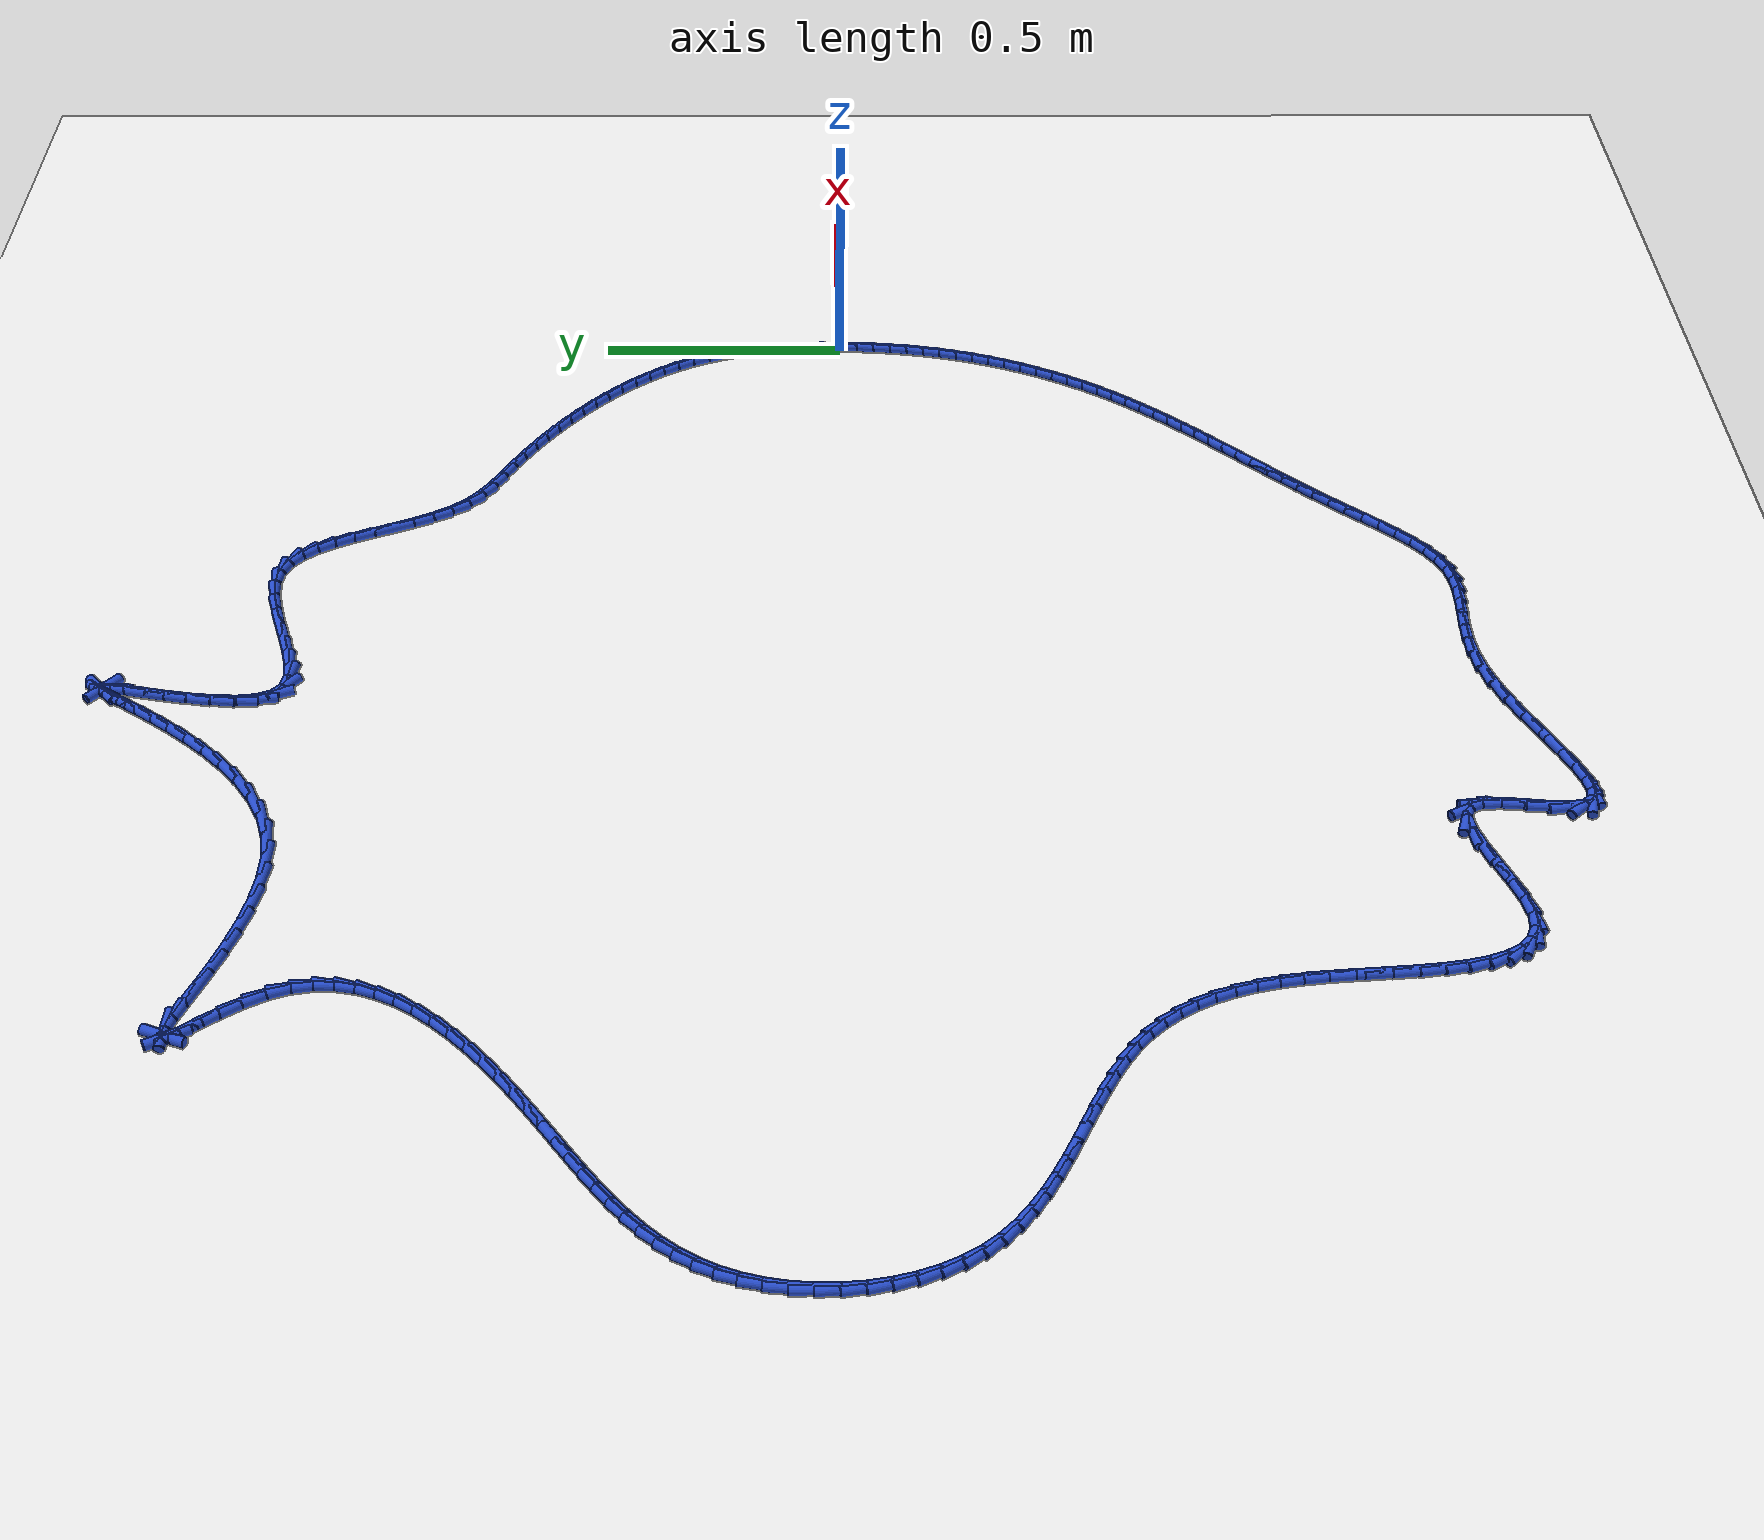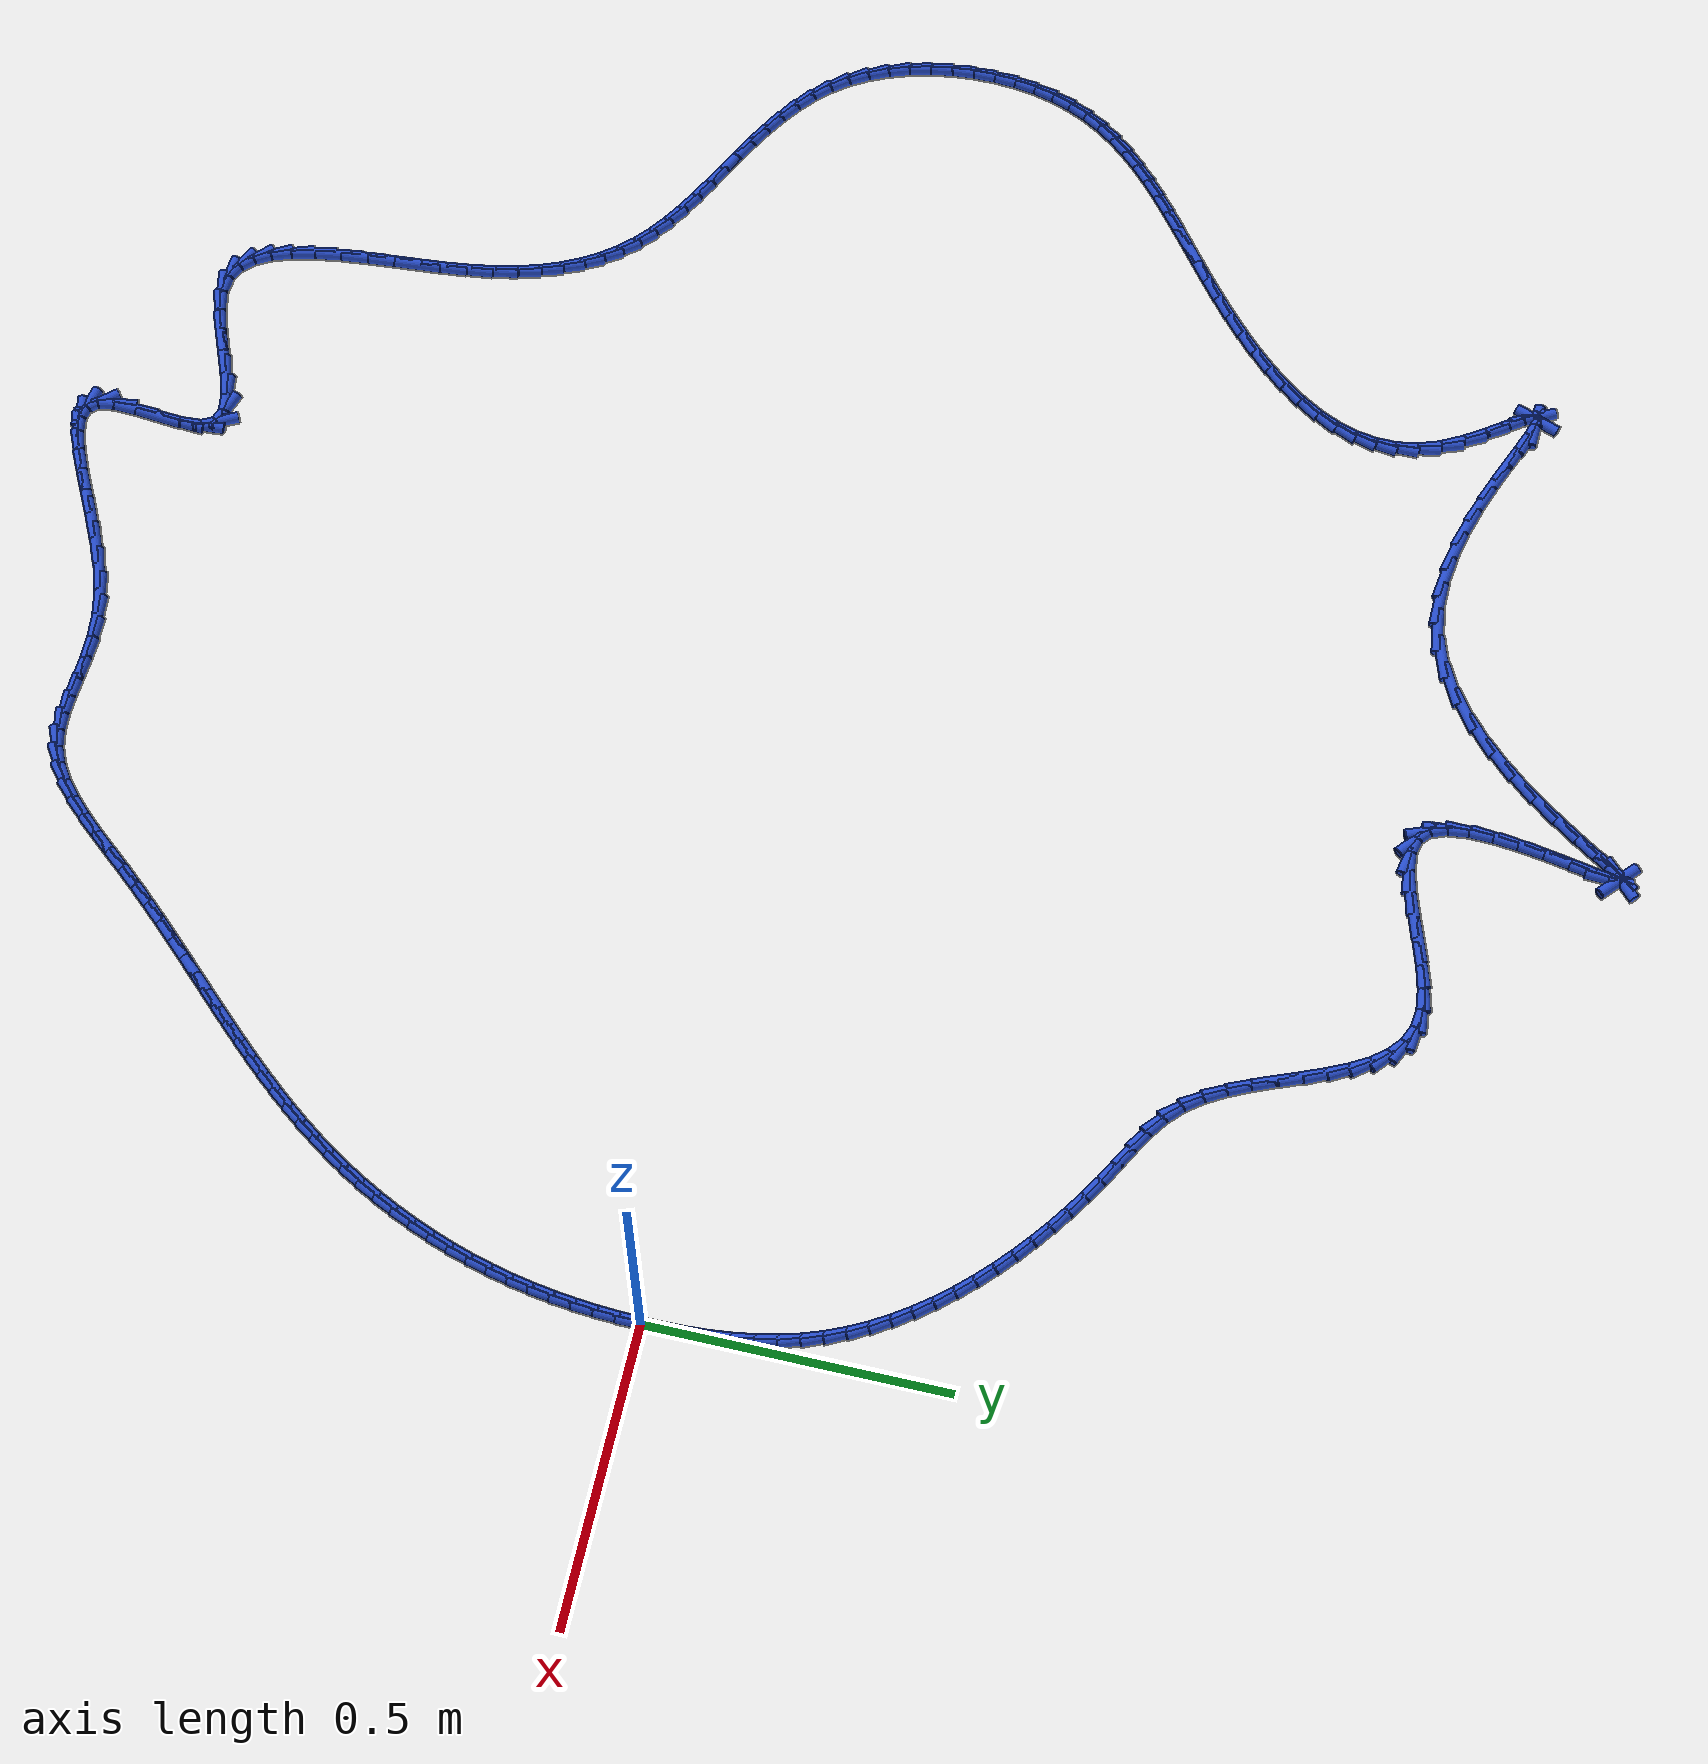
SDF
<sdf version="1.6">
 <world name="default">
  <light name="sun" type="directional">
   <pose>0 0 10 0 -0 0</pose>
   <diffuse>0.8 0.8 0.8 1</diffuse>
   <specular>0.2 0.2 0.2 1</specular>
   <attenuation>
    <range>1000</range>
    <constant>0.9</constant>
    <linear>0.01</linear>
    <quadratic>0.001</quadratic>
   </attenuation>
   <direction>-0.5 0.1 -0.9</direction>
  </light>
  <model name="ground_plane">
   <static>1</static>
   <link name="link">
    <collision name="collision">
     <geometry><plane><normal>0 0 1</normal><size>100 100</size></plane></geometry>
     <surface><friction><ode><mu>100</mu><mu2>50</mu2></ode></friction></surface>
    </collision>
    <visual name="visual">
     <cast_shadows>0</cast_shadows>
     <geometry><plane><normal>0 0 1</normal><size>100 100</size></plane></geometry>
     <material>
      <script><uri>file://media/materials/scripts/gazebo.material</uri><name>Gazebo/WhiteGlow</name></script>
     </material>
    </visual>
   </link>
  </model>
  <gravity>0 0 -9.8</gravity>
  <magnetic_field>6e-06 2.3e-05 -4.2e-05</magnetic_field>
  <atmosphere type="adiabatic"/>
  <physics name="default_physics" default="0" type="ode">
   <max_step_size>0.001</max_step_size>
   <real_time_factor>1</real_time_factor>
   <real_time_update_rate>1000</real_time_update_rate>
  </physics>
  <scene><ambient>0.4 0.4 0.4 1</ambient><background>0.7 0.7 0.7 1</background><shadows>1</shadows></scene>
  <spherical_coordinates>
   <surface_model>EARTH_WGS84</surface_model>
   <latitude_deg>0</latitude_deg>
   <longitude_deg>0</longitude_deg>
   <elevation>0</elevation>
   <heading_deg>0</heading_deg>
  </spherical_coordinates>
  <model name="line">
   <link name="link_0">
    <pose>7.37257477290143e-18 3.469446951953614e-17 0.01 0 1.57 1.5680438948402413</pose>
    <collision name="collision">
     <geometry><cylinder><radius>0.01</radius><length>0.08</length></cylinder></geometry>
    </collision>
    <visual name="visual">
     <material>
      <script><name>Gazebo/Blue</name><uri>file://media/materials/scripts/gazebo.material</uri></script>
     </material>
     <geometry><cylinder><radius>0.01</radius><length>0.08</length></cylinder></geometry>
    </visual>
   </link>
   <link name="link_1">
    <pose>0.0001003149996280971 0.03644585877352556 0.01 0 1.57 -1.541195006216087</pose>
    <collision name="collision">
     <geometry><cylinder><radius>0.01</radius><length>0.08</length></cylinder></geometry>
    </collision>
    <visual name="visual">
     <material>
      <script><name>Gazebo/Blue</name><uri>file://media/materials/scripts/gazebo.material</uri></script>
     </material>
     <geometry><cylinder><radius>0.01</radius><length>0.08</length></cylinder></geometry>
    </visual>
   </link>
   <link name="link_2">
    <pose>-0.0009796142377771593 0.0729176705978343 0.01 0 1.57 -1.5036603185891484</pose>
    <collision name="collision">
     <geometry><cylinder><radius>0.01</radius><length>0.08</length></cylinder></geometry>
    </collision>
    <visual name="visual">
     <material>
      <script><name>Gazebo/Blue</name><uri>file://media/materials/scripts/gazebo.material</uri></script>
     </material>
     <geometry><cylinder><radius>0.01</radius><length>0.08</length></cylinder></geometry>
    </visual>
   </link>
   <link name="link_3">
    <pose>-0.003423812057419353 0.10926961618761917 0.01 0 1.57 -1.4606070433337586</pose>
    <collision name="collision">
     <geometry><cylinder><radius>0.01</radius><length>0.08</length></cylinder></geometry>
    </collision>
    <visual name="visual">
     <material>
      <script><name>Gazebo/Blue</name><uri>file://media/materials/scripts/gazebo.material</uri></script>
     </material>
     <geometry><cylinder><radius>0.01</radius><length>0.08</length></cylinder></geometry>
    </visual>
   </link>
   <link name="link_4">
    <pose>-0.007416302804502077 0.14535587625757285 0.01 0 1.57 -1.411680642565094</pose>
    <collision name="collision">
     <geometry><cylinder><radius>0.01</radius><length>0.08</length></cylinder></geometry>
    </collision>
    <visual name="visual">
     <material>
      <script><name>Gazebo/Blue</name><uri>file://media/materials/scripts/gazebo.material</uri></script>
     </material>
     <geometry><cylinder><radius>0.01</radius><length>0.08</length></cylinder></geometry>
    </visual>
   </link>
   <link name="link_5">
    <pose>-0.013141110824228922 0.1810306315223883 0.01 0 1.57 -1.356547341380486</pose>
    <collision name="collision">
     <geometry><cylinder><radius>0.01</radius><length>0.08</length></cylinder></geometry>
    </collision>
    <visual name="visual">
     <material>
      <script><name>Gazebo/Blue</name><uri>file://media/materials/scripts/gazebo.material</uri></script>
     </material>
     <geometry><cylinder><radius>0.01</radius><length>0.08</length></cylinder></geometry>
    </visual>
   </link>
   <link name="link_6">
    <pose>-0.020782260461803488 0.2161480626967583 0.01 0 1.57 -1.294946770154717</pose>
    <collision name="collision">
     <geometry><cylinder><radius>0.01</radius><length>0.08</length></cylinder></geometry>
    </collision>
    <visual name="visual">
     <material>
      <script><name>Gazebo/Blue</name><uri>file://media/materials/scripts/gazebo.material</uri></script>
     </material>
     <geometry><cylinder><radius>0.01</radius><length>0.08</length></cylinder></geometry>
    </visual>
   </link>
   <link name="link_7">
    <pose>-0.030523776062429356 0.2505623504953757 0.01 0 1.57 -1.2268920229269533</pose>
    <collision name="collision">
     <geometry><cylinder><radius>0.01</radius><length>0.08</length></cylinder></geometry>
    </collision>
    <visual name="visual">
     <material>
      <script><name>Gazebo/Blue</name><uri>file://media/materials/scripts/gazebo.material</uri></script>
     </material>
     <geometry><cylinder><radius>0.01</radius><length>0.08</length></cylinder></geometry>
    </visual>
   </link>
   <link name="link_8">
    <pose>-0.04254536098203102 0.28412946136138806 0.01 0 1.57 -1.1567805826560806</pose>
    <collision name="collision">
     <geometry><cylinder><radius>0.01</radius><length>0.08</length></cylinder></geometry>
    </collision>
    <visual name="visual">
     <material>
      <script><name>Gazebo/Blue</name><uri>file://media/materials/scripts/gazebo.material</uri></script>
     </material>
     <geometry><cylinder><radius>0.01</radius><length>0.08</length></cylinder></geometry>
    </visual>
   </link>
   <link name="link_9">
    <pose>-0.05688533882825792 0.3167637895245334 0.01 0 1.57 -1.0900268088113938</pose>
    <collision name="collision">
     <geometry><cylinder><radius>0.01</radius><length>0.08</length></cylinder></geometry>
    </collision>
    <visual name="visual">
     <material>
      <script><name>Gazebo/Blue</name><uri>file://media/materials/scripts/gazebo.material</uri></script>
     </material>
     <geometry><cylinder><radius>0.01</radius><length>0.08</length></cylinder></geometry>
    </visual>
   </link>
   <link name="link_10">
    <pose>-0.07341243362507215 0.3484498193682118 0.01 0 1.57 -1.0271024939809505</pose>
    <collision name="collision">
     <geometry><cylinder><radius>0.01</radius><length>0.08</length></cylinder></geometry>
    </collision>
    <visual name="visual">
     <material>
      <script><name>Gazebo/Blue</name><uri>file://media/materials/scripts/gazebo.material</uri></script>
     </material>
     <geometry><cylinder><radius>0.01</radius><length>0.08</length></cylinder></geometry>
    </visual>
   </link>
   <link name="link_11">
    <pose>-0.09198534577649915 0.37917617772149675 0.01 0 1.57 -0.9680378404753012</pose>
    <collision name="collision">
     <geometry><cylinder><radius>0.01</radius><length>0.08</length></cylinder></geometry>
    </collision>
    <visual name="visual">
     <material>
      <script><name>Gazebo/Blue</name><uri>file://media/materials/scripts/gazebo.material</uri></script>
     </material>
     <geometry><cylinder><radius>0.01</radius><length>0.08</length></cylinder></geometry>
    </visual>
   </link>
   <link name="link_12">
    <pose>-0.1124627756865645 0.4089314914134619 0.01 0 1.57 -0.9127543947486471</pose>
    <collision name="collision">
     <geometry><cylinder><radius>0.01</radius><length>0.08</length></cylinder></geometry>
    </collision>
    <visual name="visual">
     <material>
      <script><name>Gazebo/Blue</name><uri>file://media/materials/scripts/gazebo.material</uri></script>
     </material>
     <geometry><cylinder><radius>0.01</radius><length>0.08</length></cylinder></geometry>
    </visual>
   </link>
   <link name="link_13">
    <pose>-0.13470342375929356 0.43770438727318056 0.01 0 1.57 -0.8610939117637058</pose>
    <collision name="collision">
     <geometry><cylinder><radius>0.01</radius><length>0.08</length></cylinder></geometry>
    </collision>
    <visual name="visual">
     <material>
      <script><name>Gazebo/Blue</name><uri>file://media/materials/scripts/gazebo.material</uri></script>
     </material>
     <geometry><cylinder><radius>0.01</radius><length>0.08</length></cylinder></geometry>
    </visual>
   </link>
   <link name="link_14">
    <pose>-0.15856599039871191 0.46548349212972634 0.01 0 1.57 -0.8128439553476126</pose>
    <collision name="collision">
     <geometry><cylinder><radius>0.01</radius><length>0.08</length></cylinder></geometry>
    </collision>
    <visual name="visual">
     <material>
      <script><name>Gazebo/Blue</name><uri>file://media/materials/scripts/gazebo.material</uri></script>
     </material>
     <geometry><cylinder><radius>0.01</radius><length>0.08</length></cylinder></geometry>
    </visual>
   </link>
   <link name="link_15">
    <pose>-0.183909176008845 0.49225743281217255 0.01 0 1.57 -0.7677588171883175</pose>
    <collision name="collision">
     <geometry><cylinder><radius>0.01</radius><length>0.08</length></cylinder></geometry>
    </collision>
    <visual name="visual">
     <material>
      <script><name>Gazebo/Blue</name><uri>file://media/materials/scripts/gazebo.material</uri></script>
     </material>
     <geometry><cylinder><radius>0.01</radius><length>0.08</length></cylinder></geometry>
    </visual>
   </link>
   <link name="link_16">
    <pose>-0.21059168099371825 0.5180148361495929 0.01 0 1.57 -0.7255754857384842</pose>
    <collision name="collision">
     <geometry><cylinder><radius>0.01</radius><length>0.08</length></cylinder></geometry>
    </collision>
    <visual name="visual">
     <material>
      <script><name>Gazebo/Blue</name><uri>file://media/materials/scripts/gazebo.material</uri></script>
     </material>
     <geometry><cylinder><radius>0.01</radius><length>0.08</length></cylinder></geometry>
    </visual>
   </link>
   <link name="link_17">
    <pose>-0.23847220575735723 0.5427443289710607 0.01 0 1.57 -0.6860250698542992</pose>
    <collision name="collision">
     <geometry><cylinder><radius>0.01</radius><length>0.08</length></cylinder></geometry>
    </collision>
    <visual name="visual">
     <material>
      <script><name>Gazebo/Blue</name><uri>file://media/materials/scripts/gazebo.material</uri></script>
     </material>
     <geometry><cylinder><radius>0.01</radius><length>0.08</length></cylinder></geometry>
    </visual>
   </link>
   <link name="link_18">
    <pose>-0.2674094507037874 0.5664345381056497 0.01 0 1.57 -0.6488403851450412</pose>
    <collision name="collision">
     <geometry><cylinder><radius>0.01</radius><length>0.08</length></cylinder></geometry>
    </collision>
    <visual name="visual">
     <material>
      <script><name>Gazebo/Blue</name><uri>file://media/materials/scripts/gazebo.material</uri></script>
     </material>
     <geometry><cylinder><radius>0.01</radius><length>0.08</length></cylinder></geometry>
    </visual>
   </link>
   <link name="link_19">
    <pose>-0.2972621162370341 0.589074090382433 0.01 0 1.57 -0.6137604726472918</pose>
    <collision name="collision">
     <geometry><cylinder><radius>0.01</radius><length>0.08</length></cylinder></geometry>
    </collision>
    <visual name="visual">
     <material>
      <script><name>Gazebo/Blue</name><uri>file://media/materials/scripts/gazebo.material</uri></script>
     </material>
     <geometry><cylinder><radius>0.01</radius><length>0.08</length></cylinder></geometry>
    </visual>
   </link>
   <link name="link_20">
    <pose>-0.327888902761123 0.6106516126304845 0.01 0 1.57 -0.5805327473783956</pose>
    <collision name="collision">
     <geometry><cylinder><radius>0.01</radius><length>0.08</length></cylinder></geometry>
    </collision>
    <visual name="visual">
     <material>
      <script><name>Gazebo/Blue</name><uri>file://media/materials/scripts/gazebo.material</uri></script>
     </material>
     <geometry><cylinder><radius>0.01</radius><length>0.08</length></cylinder></geometry>
    </visual>
   </link>
   <link name="link_21">
    <pose>-0.35914851068007947 0.6311557316788774 0.01 0 1.57 -0.5489133423862994</pose>
    <collision name="collision">
     <geometry><cylinder><radius>0.01</radius><length>0.08</length></cylinder></geometry>
    </collision>
    <visual name="visual">
     <material>
      <script><name>Gazebo/Blue</name><uri>file://media/materials/scripts/gazebo.material</uri></script>
     </material>
     <geometry><cylinder><radius>0.01</radius><length>0.08</length></cylinder></geometry>
    </visual>
   </link>
   <link name="link_22">
    <pose>-0.390899640397929 0.6505750743566852 0.01 0 1.57 -0.5186660651034908</pose>
    <collision name="collision">
     <geometry><cylinder><radius>0.01</radius><length>0.08</length></cylinder></geometry>
    </collision>
    <visual name="visual">
     <material>
      <script><name>Gazebo/Blue</name><uri>file://media/materials/scripts/gazebo.material</uri></script>
     </material>
     <geometry><cylinder><radius>0.01</radius><length>0.08</length></cylinder></geometry>
    </visual>
   </link>
   <link name="link_23">
    <pose>-0.42300099231869714 0.6688982674929815 0.01 0 1.57 -0.49745060301187355</pose>
    <collision name="collision">
     <geometry><cylinder><radius>0.01</radius><length>0.08</length></cylinder></geometry>
    </collision>
    <visual name="visual">
     <material>
      <script><name>Gazebo/Blue</name><uri>file://media/materials/scripts/gazebo.material</uri></script>
     </material>
     <geometry><cylinder><radius>0.01</radius><length>0.08</length></cylinder></geometry>
    </visual>
   </link>
   <link name="link_24">
    <pose>-0.45517577425606764 0.6863690721309254 0.01 0 1.57 -0.5217485570939469</pose>
    <collision name="collision">
     <geometry><cylinder><radius>0.01</radius><length>0.08</length></cylinder></geometry>
    </collision>
    <visual name="visual">
     <material>
      <script><name>Gazebo/Blue</name><uri>file://media/materials/scripts/gazebo.material</uri></script>
     </material>
     <geometry><cylinder><radius>0.01</radius><length>0.08</length></cylinder></geometry>
    </visual>
   </link>
   <link name="link_25">
    <pose>-0.4865296979349367 0.7043940020436651 0.01 0 1.57 -0.6036882795614128</pose>
    <collision name="collision">
     <geometry><cylinder><radius>0.01</radius><length>0.08</length></cylinder></geometry>
    </collision>
    <visual name="visual">
     <material>
      <script><name>Gazebo/Blue</name><uri>file://media/materials/scripts/gazebo.material</uri></script>
     </material>
     <geometry><cylinder><radius>0.01</radius><length>0.08</length></cylinder></geometry>
    </visual>
   </link>
   <link name="link_26">
    <pose>-0.5159926603953607 0.7247106322183118 0.01 0 1.57 -0.7430085725916532</pose>
    <collision name="collision">
     <geometry><cylinder><radius>0.01</radius><length>0.08</length></cylinder></geometry>
    </collision>
    <visual name="visual">
     <material>
      <script><name>Gazebo/Blue</name><uri>file://media/materials/scripts/gazebo.material</uri></script>
     </material>
     <geometry><cylinder><radius>0.01</radius><length>0.08</length></cylinder></geometry>
    </visual>
   </link>
   <link name="link_27">
    <pose>-0.5424948299959679 0.7490560993720549 0.01 0 1.57 -0.9101919167858923</pose>
    <collision name="collision">
     <geometry><cylinder><radius>0.01</radius><length>0.08</length></cylinder></geometry>
    </collision>
    <visual name="visual">
     <material>
      <script><name>Gazebo/Blue</name><uri>file://media/materials/scripts/gazebo.material</uri></script>
     </material>
     <geometry><cylinder><radius>0.01</radius><length>0.08</length></cylinder></geometry>
    </visual>
   </link>
   <link name="link_28">
    <pose>-0.5653758503830528 0.7785012039356963 0.01 0 1.57 -1.0379359335360465</pose>
    <collision name="collision">
     <geometry><cylinder><radius>0.01</radius><length>0.08</length></cylinder></geometry>
    </collision>
    <visual name="visual">
     <material>
      <script><name>Gazebo/Blue</name><uri>file://media/materials/scripts/gazebo.material</uri></script>
     </material>
     <geometry><cylinder><radius>0.01</radius><length>0.08</length></cylinder></geometry>
    </visual>
   </link>
   <link name="link_29">
    <pose>-0.5852027410874225 0.8121194461035615 0.01 0 1.57 -1.1221076226531532</pose>
    <collision name="collision">
     <geometry><cylinder><radius>0.01</radius><length>0.08</length></cylinder></geometry>
    </collision>
    <visual name="visual">
     <material>
      <script><name>Gazebo/Blue</name><uri>file://media/materials/scripts/gazebo.material</uri></script>
     </material>
     <geometry><cylinder><radius>0.01</radius><length>0.08</length></cylinder></geometry>
    </visual>
   </link>
   <link name="link_30">
    <pose>-0.6027715189691599 0.8486116803094669 0.01 0 1.57 -1.1705249542729292</pose>
    <collision name="collision">
     <geometry><cylinder><radius>0.01</radius><length>0.08</length></cylinder></geometry>
    </collision>
    <visual name="visual">
     <material>
      <script><name>Gazebo/Blue</name><uri>file://media/materials/scripts/gazebo.material</uri></script>
     </material>
     <geometry><cylinder><radius>0.01</radius><length>0.08</length></cylinder></geometry>
    </visual>
   </link>
   <link name="link_31">
    <pose>-0.6188782008883477 0.8866787609872284 0.01 0 1.57 -1.1879653254964875</pose>
    <collision name="collision">
     <geometry><cylinder><radius>0.01</radius><length>0.08</length></cylinder></geometry>
    </collision>
    <visual name="visual">
     <material>
      <script><name>Gazebo/Blue</name><uri>file://media/materials/scripts/gazebo.material</uri></script>
     </material>
     <geometry><cylinder><radius>0.01</radius><length>0.08</length></cylinder></geometry>
    </visual>
   </link>
   <link name="link_32">
    <pose>-0.6343188037050683 0.9250215425706622 0.01 0 1.57 -1.1755300130543112</pose>
    <collision name="collision">
     <geometry><cylinder><radius>0.01</radius><length>0.08</length></cylinder></geometry>
    </collision>
    <visual name="visual">
     <material>
      <script><name>Gazebo/Blue</name><uri>file://media/materials/scripts/gazebo.material</uri></script>
     </material>
     <geometry><cylinder><radius>0.01</radius><length>0.08</length></cylinder></geometry>
    </visual>
   </link>
   <link name="link_33">
    <pose>-0.6498893442794046 0.9623408794935835 0.01 0 1.57 -1.130312068448243</pose>
    <collision name="collision">
     <geometry><cylinder><radius>0.01</radius><length>0.08</length></cylinder></geometry>
    </collision>
    <visual name="visual">
     <material>
      <script><name>Gazebo/Blue</name><uri>file://media/materials/scripts/gazebo.material</uri></script>
     </material>
     <geometry><cylinder><radius>0.01</radius><length>0.08</length></cylinder></geometry>
    </visual>
   </link>
   <link name="link_34">
    <pose>-0.6663858394714394 0.9973376261898089 0.01 0 1.57 -1.044712783987775</pose>
    <collision name="collision">
     <geometry><cylinder><radius>0.01</radius><length>0.08</length></cylinder></geometry>
    </collision>
    <visual name="visual">
     <material>
      <script><name>Gazebo/Blue</name><uri>file://media/materials/scripts/gazebo.material</uri></script>
     </material>
     <geometry><cylinder><radius>0.01</radius><length>0.08</length></cylinder></geometry>
    </visual>
   </link>
   <link name="link_35">
    <pose>-0.6846043061412549 1.028712637093154 0.01 0 1.57 -0.9059717873614976</pose>
    <collision name="collision">
     <geometry><cylinder><radius>0.01</radius><length>0.08</length></cylinder></geometry>
    </collision>
    <visual name="visual">
     <material>
      <script><name>Gazebo/Blue</name><uri>file://media/materials/scripts/gazebo.material</uri></script>
     </material>
     <geometry><cylinder><radius>0.01</radius><length>0.08</length></cylinder></geometry>
    </visual>
   </link>
   <link name="link_36">
    <pose>-0.7053407611489346 1.0551667666374356 0.01 0 1.57 -0.6994324989188095</pose>
    <collision name="collision">
     <geometry><cylinder><radius>0.01</radius><length>0.08</length></cylinder></geometry>
    </collision>
    <visual name="visual">
     <material>
      <script><name>Gazebo/Blue</name><uri>file://media/materials/scripts/gazebo.material</uri></script>
     </material>
     <geometry><cylinder><radius>0.01</radius><length>0.08</length></cylinder></geometry>
    </visual>
   </link>
   <link name="link_37">
    <pose>-0.7293912213545606 1.0754008692564685 0.01 0 1.57 -0.42411456107680556</pose>
    <collision name="collision">
     <geometry><cylinder><radius>0.01</radius><length>0.08</length></cylinder></geometry>
    </collision>
    <visual name="visual">
     <material>
      <script><name>Gazebo/Blue</name><uri>file://media/materials/scripts/gazebo.material</uri></script>
     </material>
     <geometry><cylinder><radius>0.01</radius><length>0.08</length></cylinder></geometry>
    </visual>
   </link>
   <link name="link_38">
    <pose>-0.7575517036182158 1.08811579938407 0.01 0 1.57 -0.12081651928637793</pose>
    <collision name="collision">
     <geometry><cylinder><radius>0.01</radius><length>0.08</length></cylinder></geometry>
    </collision>
    <visual name="visual">
     <material>
      <script><name>Gazebo/Blue</name><uri>file://media/materials/scripts/gazebo.material</uri></script>
     </material>
     <geometry><cylinder><radius>0.01</radius><length>0.08</length></cylinder></geometry>
    </visual>
   </link>
   <link name="link_39">
    <pose>-0.79054943366285 1.092121981521475 0.01 0 1.57 0.10658094657249761</pose>
    <collision name="collision">
     <geometry><cylinder><radius>0.01</radius><length>0.08</length></cylinder></geometry>
    </collision>
    <visual name="visual">
     <material>
      <script><name>Gazebo/Blue</name><uri>file://media/materials/scripts/gazebo.material</uri></script>
     </material>
     <geometry><cylinder><radius>0.01</radius><length>0.08</length></cylinder></geometry>
    </visual>
   </link>
   <link name="link_40">
    <pose>-0.8279227131867954 1.0881235504786053 0.01 0 1.57 0.23627785186078104</pose>
    <collision name="collision">
     <geometry><cylinder><radius>0.01</radius><length>0.08</length></cylinder></geometry>
    </collision>
    <visual name="visual">
     <material>
      <script><name>Gazebo/Blue</name><uri>file://media/materials/scripts/gazebo.material</uri></script>
     </material>
     <geometry><cylinder><radius>0.01</radius><length>0.08</length></cylinder></geometry>
    </visual>
   </link>
   <link name="link_41">
    <pose>-0.8682054258702996 1.0784244714293816 0.01 0 1.57 0.30323379472429</pose>
    <collision name="collision">
     <geometry><cylinder><radius>0.01</radius><length>0.08</length></cylinder></geometry>
    </collision>
    <visual name="visual">
     <material>
      <script><name>Gazebo/Blue</name><uri>file://media/materials/scripts/gazebo.material</uri></script>
     </material>
     <geometry><cylinder><radius>0.01</radius><length>0.08</length></cylinder></geometry>
    </visual>
   </link>
   <link name="link_42">
    <pose>-0.9098998947503801 1.0653789791311443 0.01 0 1.57 0.3253833499726771</pose>
    <collision name="collision">
     <geometry><cylinder><radius>0.01</radius><length>0.08</length></cylinder></geometry>
    </collision>
    <visual name="visual">
     <material>
      <script><name>Gazebo/Blue</name><uri>file://media/materials/scripts/gazebo.material</uri></script>
     </material>
     <geometry><cylinder><radius>0.01</radius><length>0.08</length></cylinder></geometry>
    </visual>
   </link>
   <link name="link_43">
    <pose>-0.9515084428640542 1.0513413083412344 0.01 0 1.57 0.3067000916274043</pose>
    <collision name="collision">
     <geometry><cylinder><radius>0.01</radius><length>0.08</length></cylinder></geometry>
    </collision>
    <visual name="visual">
     <material>
      <script><name>Gazebo/Blue</name><uri>file://media/materials/scripts/gazebo.material</uri></script>
     </material>
     <geometry><cylinder><radius>0.01</radius><length>0.08</length></cylinder></geometry>
    </visual>
   </link>
   <link name="link_44">
    <pose>-0.9915333932483394 1.0386656938169918 0.01 0 1.57 0.23791980464423504</pose>
    <collision name="collision">
     <geometry><cylinder><radius>0.01</radius><length>0.08</length></cylinder></geometry>
    </collision>
    <visual name="visual">
     <material>
      <script><name>Gazebo/Blue</name><uri>file://media/materials/scripts/gazebo.material</uri></script>
     </material>
     <geometry><cylinder><radius>0.01</radius><length>0.08</length></cylinder></geometry>
    </visual>
   </link>
   <link name="link_45">
    <pose>-1.0284770689402536 1.0297063703157576 0.01 0 1.57 0.08902169457782318</pose>
    <collision name="collision">
     <geometry><cylinder><radius>0.01</radius><length>0.08</length></cylinder></geometry>
    </collision>
    <visual name="visual">
     <material>
      <script><name>Gazebo/Blue</name><uri>file://media/materials/scripts/gazebo.material</uri></script>
     </material>
     <geometry><cylinder><radius>0.01</radius><length>0.08</length></cylinder></geometry>
    </visual>
   </link>
   <link name="link_46">
    <pose>-1.0608417929768135 1.0268175725948727 0.01 0 1.57 -0.2075554879373817</pose>
    <collision name="collision">
     <geometry><cylinder><radius>0.01</radius><length>0.08</length></cylinder></geometry>
    </collision>
    <visual name="visual">
     <material>
      <script><name>Gazebo/Blue</name><uri>file://media/materials/scripts/gazebo.material</uri></script>
     </material>
     <geometry><cylinder><radius>0.01</radius><length>0.08</length></cylinder></geometry>
    </visual>
   </link>
   <link name="link_47">
    <pose>-1.0871298883950369 1.0323535354116766 0.01 0 1.57 -0.7159685127380863</pose>
    <collision name="collision">
     <geometry><cylinder><radius>0.01</radius><length>0.08</length></cylinder></geometry>
    </collision>
    <visual name="visual">
     <material>
      <script><name>Gazebo/Blue</name><uri>file://media/materials/scripts/gazebo.material</uri></script>
     </material>
     <geometry><cylinder><radius>0.01</radius><length>0.08</length></cylinder></geometry>
    </visual>
   </link>
   <link name="link_48">
    <pose>-1.1058568845556664 1.0486452784578446 0.01 0 1.57 -1.1997037790207523</pose>
    <collision name="collision">
     <geometry><cylinder><radius>0.01</radius><length>0.08</length></cylinder></geometry>
    </collision>
    <visual name="visual">
     <material>
      <script><name>Gazebo/Blue</name><uri>file://media/materials/scripts/gazebo.material</uri></script>
     </material>
     <geometry><cylinder><radius>0.01</radius><length>0.08</length></cylinder></geometry>
    </visual>
   </link>
   <link name="link_49">
    <pose>-1.116577707339217 1.0761966923192445 0.01 0 1.57 -1.4596148018771482</pose>
    <collision name="collision">
     <geometry><cylinder><radius>0.01</radius><length>0.08</length></cylinder></geometry>
    </collision>
    <visual name="visual">
     <material>
      <script><name>Gazebo/Blue</name><uri>file://media/materials/scripts/gazebo.material</uri></script>
     </material>
     <geometry><cylinder><radius>0.01</radius><length>0.08</length></cylinder></geometry>
    </visual>
   </link>
   <link name="link_50">
    <pose>-1.120619169354247 1.1123969122872868 0.01 0 1.57 1.5436608416807422</pose>
    <collision name="collision">
     <geometry><cylinder><radius>0.01</radius><length>0.08</length></cylinder></geometry>
    </collision>
    <visual name="visual">
     <material>
      <script><name>Gazebo/Blue</name><uri>file://media/materials/scripts/gazebo.material</uri></script>
     </material>
     <geometry><cylinder><radius>0.01</radius><length>0.08</length></cylinder></geometry>
    </visual>
   </link>
   <link name="link_51">
    <pose>-1.1194809845084055 1.1543311347907883 0.01 0 1.57 1.4635501939387812</pose>
    <collision name="collision">
     <geometry><cylinder><radius>0.01</radius><length>0.08</length></cylinder></geometry>
    </collision>
    <visual name="visual">
     <material>
      <script><name>Gazebo/Blue</name><uri>file://media/materials/scripts/gazebo.material</uri></script>
     </material>
     <geometry><cylinder><radius>0.01</radius><length>0.08</length></cylinder></geometry>
    </visual>
   </link>
   <link name="link_52">
    <pose>-1.1146628667093426 1.199084556258569 0.01 0 1.57 1.4153503527048863</pose>
    <collision name="collision">
     <geometry><cylinder><radius>0.01</radius><length>0.08</length></cylinder></geometry>
    </collision>
    <visual name="visual">
     <material>
      <script><name>Gazebo/Blue</name><uri>file://media/materials/scripts/gazebo.material</uri></script>
     </material>
     <geometry><cylinder><radius>0.01</radius><length>0.08</length></cylinder></geometry>
    </visual>
   </link>
   <link name="link_53">
    <pose>-1.107664529864707 1.2437423731194464 0.01 0 1.57 1.3884665997531134</pose>
    <collision name="collision">
     <geometry><cylinder><radius>0.01</radius><length>0.08</length></cylinder></geometry>
    </collision>
    <visual name="visual">
     <material>
      <script><name>Gazebo/Blue</name><uri>file://media/materials/scripts/gazebo.material</uri></script>
     </material>
     <geometry><cylinder><radius>0.01</radius><length>0.08</length></cylinder></geometry>
    </visual>
   </link>
   <link name="link_54">
    <pose>-1.0999856878821483 1.2853897818022402 0.01 0 1.57 1.3810785484940047</pose>
    <collision name="collision">
     <geometry><cylinder><radius>0.01</radius><length>0.08</length></cylinder></geometry>
    </collision>
    <visual name="visual">
     <material>
      <script><name>Gazebo/Blue</name><uri>file://media/materials/scripts/gazebo.material</uri></script>
     </material>
     <geometry><cylinder><radius>0.01</radius><length>0.08</length></cylinder></geometry>
    </visual>
   </link>
   <link name="link_55">
    <pose>-1.093126054669316 1.3211119787357677 0.01 0 1.57 1.4034642523657805</pose>
    <collision name="collision">
     <geometry><cylinder><radius>0.01</radius><length>0.08</length></cylinder></geometry>
    </collision>
    <visual name="visual">
     <material>
      <script><name>Gazebo/Blue</name><uri>file://media/materials/scripts/gazebo.material</uri></script>
     </material>
     <geometry><cylinder><radius>0.01</radius><length>0.08</length></cylinder></geometry>
    </visual>
   </link>
   <link name="link_56">
    <pose>-1.0885853441338587 1.3479941603488486 0.01 0 1.57 1.5201099779218397</pose>
    <collision name="collision">
     <geometry><cylinder><radius>0.01</radius><length>0.08</length></cylinder></geometry>
    </collision>
    <visual name="visual">
     <material>
      <script><name>Gazebo/Blue</name><uri>file://media/materials/scripts/gazebo.material</uri></script>
     </material>
     <geometry><cylinder><radius>0.01</radius><length>0.08</length></cylinder></geometry>
    </visual>
   </link>
   <link name="link_57">
    <pose>-1.0878107086369837 1.3632639919086096 0.01 0 1.57 -0.7328079389996761</pose>
    <collision name="collision">
     <geometry><cylinder><radius>0.01</radius><length>0.08</length></cylinder></geometry>
    </collision>
    <visual name="visual">
     <material>
      <script><name>Gazebo/Blue</name><uri>file://media/materials/scripts/gazebo.material</uri></script>
     </material>
     <geometry><cylinder><radius>0.01</radius><length>0.08</length></cylinder></geometry>
    </visual>
   </link>
   <link name="link_58">
    <pose>-1.0913880550065913 1.3664835572625327 0.01 0 1.57 0.7557595258914901</pose>
    <collision name="collision">
     <geometry><cylinder><radius>0.01</radius><length>0.08</length></cylinder></geometry>
    </collision>
    <visual name="visual">
     <material>
      <script><name>Gazebo/Blue</name><uri>file://media/materials/scripts/gazebo.material</uri></script>
     </material>
     <geometry><cylinder><radius>0.01</radius><length>0.08</length></cylinder></geometry>
    </visual>
   </link>
   <link name="link_59">
    <pose>-1.0991998512193764 1.3591216215248256 0.01 0 1.57 0.9433103808243845</pose>
    <collision name="collision">
     <geometry><cylinder><radius>0.01</radius><length>0.08</length></cylinder></geometry>
    </collision>
    <visual name="visual">
     <material>
      <script><name>Gazebo/Blue</name><uri>file://media/materials/scripts/gazebo.material</uri></script>
     </material>
     <geometry><cylinder><radius>0.01</radius><length>0.08</length></cylinder></geometry>
    </visual>
   </link>
   <link name="link_60">
    <pose>-1.1111079708956262 1.342702771113125 0.01 0 1.57 0.9857227454308445</pose>
    <collision name="collision">
     <geometry><cylinder><radius>0.01</radius><length>0.08</length></cylinder></geometry>
    </collision>
    <visual name="visual">
     <material>
      <script><name>Gazebo/Blue</name><uri>file://media/materials/scripts/gazebo.material</uri></script>
     </material>
     <geometry><cylinder><radius>0.01</radius><length>0.08</length></cylinder></geometry>
    </visual>
   </link>
   <link name="link_61">
    <pose>-1.1269742876556303 1.3187515924450675 0.01 0 1.57 0.9894371976624968</pose>
    <collision name="collision">
     <geometry><cylinder><radius>0.01</radius><length>0.08</length></cylinder></geometry>
    </collision>
    <visual name="visual">
     <material>
      <script><name>Gazebo/Blue</name><uri>file://media/materials/scripts/gazebo.material</uri></script>
     </material>
     <geometry><cylinder><radius>0.01</radius><length>0.08</length></cylinder></geometry>
    </visual>
   </link>
   <link name="link_62">
    <pose>-1.1466606751196768 1.288792671938291 0.01 0 1.57 0.9746583570370749</pose>
    <collision name="collision">
     <geometry><cylinder><radius>0.01</radius><length>0.08</length></cylinder></geometry>
    </collision>
    <visual name="visual">
     <material>
      <script><name>Gazebo/Blue</name><uri>file://media/materials/scripts/gazebo.material</uri></script>
     </material>
     <geometry><cylinder><radius>0.01</radius><length>0.08</length></cylinder></geometry>
    </visual>
   </link>
   <link name="link_63">
    <pose>-1.1700290069080548 1.2543505960104315 0.01 0 1.57 0.9470606173593883</pose>
    <collision name="collision">
     <geometry><cylinder><radius>0.01</radius><length>0.08</length></cylinder></geometry>
    </collision>
    <visual name="visual">
     <material>
      <script><name>Gazebo/Blue</name><uri>file://media/materials/scripts/gazebo.material</uri></script>
     </material>
     <geometry><cylinder><radius>0.01</radius><length>0.08</length></cylinder></geometry>
    </visual>
   </link>
   <link name="link_64">
    <pose>-1.1969411566410522 1.2169499510791275 0.01 0 1.57 0.9079406036954891</pose>
    <collision name="collision">
     <geometry><cylinder><radius>0.01</radius><length>0.08</length></cylinder></geometry>
    </collision>
    <visual name="visual">
     <material>
      <script><name>Gazebo/Blue</name><uri>file://media/materials/scripts/gazebo.material</uri></script>
     </material>
     <geometry><cylinder><radius>0.01</radius><length>0.08</length></cylinder></geometry>
    </visual>
   </link>
   <link name="link_65">
    <pose>-1.2272589979389572 1.1781153235620145 0.01 0 1.57 0.8565987383460771</pose>
    <collision name="collision">
     <geometry><cylinder><radius>0.01</radius><length>0.08</length></cylinder></geometry>
    </collision>
    <visual name="visual">
     <material>
      <script><name>Gazebo/Blue</name><uri>file://media/materials/scripts/gazebo.material</uri></script>
     </material>
     <geometry><cylinder><radius>0.01</radius><length>0.08</length></cylinder></geometry>
    </visual>
   </link>
   <link name="link_66">
    <pose>-1.2608444044220597 1.1393712998767298 0.01 0 1.57 0.7910043820636863</pose>
    <collision name="collision">
     <geometry><cylinder><radius>0.01</radius><length>0.08</length></cylinder></geometry>
    </collision>
    <visual name="visual">
     <material>
      <script><name>Gazebo/Blue</name><uri>file://media/materials/scripts/gazebo.material</uri></script>
     </material>
     <geometry><cylinder><radius>0.01</radius><length>0.08</length></cylinder></geometry>
    </visual>
   </link>
   <link name="link_67">
    <pose>-1.2975592497106474 1.1022424664409118 0.01 0 1.57 0.7079755903735994</pose>
    <collision name="collision">
     <geometry><cylinder><radius>0.01</radius><length>0.08</length></cylinder></geometry>
    </collision>
    <visual name="visual">
     <material>
      <script><name>Gazebo/Blue</name><uri>file://media/materials/scripts/gazebo.material</uri></script>
     </material>
     <geometry><cylinder><radius>0.01</radius><length>0.08</length></cylinder></geometry>
    </visual>
   </link>
   <link name="link_68">
    <pose>-1.3372654074250094 1.0682534096721956 0.01 0 1.57 0.6033260060816759</pose>
    <collision name="collision">
     <geometry><cylinder><radius>0.01</radius><length>0.08</length></cylinder></geometry>
    </collision>
    <visual name="visual">
     <material>
      <script><name>Gazebo/Blue</name><uri>file://media/materials/scripts/gazebo.material</uri></script>
     </material>
     <geometry><cylinder><radius>0.01</radius><length>0.08</length></cylinder></geometry>
    </visual>
   </link>
   <link name="link_69">
    <pose>-1.3798247511854336 1.0389287159882197 0.01 0 1.57 0.4724180123842401</pose>
    <collision name="collision">
     <geometry><cylinder><radius>0.01</radius><length>0.08</length></cylinder></geometry>
    </collision>
    <visual name="visual">
     <material>
      <script><name>Gazebo/Blue</name><uri>file://media/materials/scripts/gazebo.material</uri></script>
     </material>
     <geometry><cylinder><radius>0.01</radius><length>0.08</length></cylinder></geometry>
    </visual>
   </link>
   <link name="link_70">
    <pose>-1.4250991546122092 1.01579297180662 0.01 0 1.57 0.31178265190740534</pose>
    <collision name="collision">
     <geometry><cylinder><radius>0.01</radius><length>0.08</length></cylinder></geometry>
    </collision>
    <visual name="visual">
     <material>
      <script><name>Gazebo/Blue</name><uri>file://media/materials/scripts/gazebo.material</uri></script>
     </material>
     <geometry><cylinder><radius>0.01</radius><length>0.08</length></cylinder></geometry>
    </visual>
   </link>
   <link name="link_71">
    <pose>-1.4729504913256237 1.0003707635450345 0.01 0 1.57 0.1321042824551783</pose>
    <collision name="collision">
     <geometry><cylinder><radius>0.01</radius><length>0.08</length></cylinder></geometry>
    </collision>
    <visual name="visual">
     <material>
      <script><name>Gazebo/Blue</name><uri>file://media/materials/scripts/gazebo.material</uri></script>
     </material>
     <geometry><cylinder><radius>0.01</radius><length>0.08</length></cylinder></geometry>
    </visual>
   </link>
   <link name="link_72">
    <pose>-1.5230870449821932 0.9937087105716411 0.01 0 1.57 -0.02119591381346585</pose>
    <collision name="collision">
     <geometry><cylinder><radius>0.01</radius><length>0.08</length></cylinder></geometry>
    </collision>
    <visual name="visual">
     <material>
      <script><name>Gazebo/Blue</name><uri>file://media/materials/scripts/gazebo.material</uri></script>
     </material>
     <geometry><cylinder><radius>0.01</radius><length>0.08</length></cylinder></geometry>
    </visual>
   </link>
   <link name="link_73">
    <pose>-1.574557194821243 0.9947998308378465 0.01 0 1.57 -0.14007135699304443</pose>
    <collision name="collision">
     <geometry><cylinder><radius>0.01</radius><length>0.08</length></cylinder></geometry>
    </collision>
    <visual name="visual">
     <material>
      <script><name>Gazebo/Blue</name><uri>file://media/materials/scripts/gazebo.material</uri></script>
     </material>
     <geometry><cylinder><radius>0.01</radius><length>0.08</length></cylinder></geometry>
    </visual>
   </link>
   <link name="link_74">
    <pose>-1.6262321262393904 1.0020857207301237 0.01 0 1.57 -0.23073331540294398</pose>
    <collision name="collision">
     <geometry><cylinder><radius>0.01</radius><length>0.08</length></cylinder></geometry>
    </collision>
    <visual name="visual">
     <material>
      <script><name>Gazebo/Blue</name><uri>file://media/materials/scripts/gazebo.material</uri></script>
     </material>
     <geometry><cylinder><radius>0.01</radius><length>0.08</length></cylinder></geometry>
    </visual>
   </link>
   <link name="link_75">
    <pose>-1.6769830223988063 1.014007969681426 0.01 0 1.57 -0.2988024923763899</pose>
    <collision name="collision">
     <geometry><cylinder><radius>0.01</radius><length>0.08</length></cylinder></geometry>
    </collision>
    <visual name="visual">
     <material>
      <script><name>Gazebo/Blue</name><uri>file://media/materials/scripts/gazebo.material</uri></script>
     </material>
     <geometry><cylinder><radius>0.01</radius><length>0.08</length></cylinder></geometry>
    </visual>
   </link>
   <link name="link_76">
    <pose>-1.7256810664616629 1.0290081671247053 0.01 0 1.57 -0.3481562601427993</pose>
    <collision name="collision">
     <geometry><cylinder><radius>0.01</radius><length>0.08</length></cylinder></geometry>
    </collision>
    <visual name="visual">
     <material>
      <script><name>Gazebo/Blue</name><uri>file://media/materials/scripts/gazebo.material</uri></script>
     </material>
     <geometry><cylinder><radius>0.01</radius><length>0.08</length></cylinder></geometry>
    </visual>
   </link>
   <link name="link_77">
    <pose>-1.7711974415901337 1.0455279024929165 0.01 0 1.57 -0.38047514130576765</pose>
    <collision name="collision">
     <geometry><cylinder><radius>0.01</radius><length>0.08</length></cylinder></geometry>
    </collision>
    <visual name="visual">
     <material>
      <script><name>Gazebo/Blue</name><uri>file://media/materials/scripts/gazebo.material</uri></script>
     </material>
     <geometry><cylinder><radius>0.01</radius><length>0.08</length></cylinder></geometry>
    </visual>
   </link>
   <link name="link_78">
    <pose>-1.812403330946388 1.0620087652190109 0.01 0 1.57 -0.3943344640666873</pose>
    <collision name="collision">
     <geometry><cylinder><radius>0.01</radius><length>0.08</length></cylinder></geometry>
    </collision>
    <visual name="visual">
     <material>
      <script><name>Gazebo/Blue</name><uri>file://media/materials/scripts/gazebo.material</uri></script>
     </material>
     <geometry><cylinder><radius>0.01</radius><length>0.08</length></cylinder></geometry>
    </visual>
   </link>
   <link name="link_79">
    <pose>-1.8481699176926 1.0768923447359424 0.01 0 1.57 -0.38193745795643896</pose>
    <collision name="collision">
     <geometry><cylinder><radius>0.01</radius><length>0.08</length></cylinder></geometry>
    </collision>
    <visual name="visual">
     <material>
      <script><name>Gazebo/Blue</name><uri>file://media/materials/scripts/gazebo.material</uri></script>
     </material>
     <geometry><cylinder><radius>0.01</radius><length>0.08</length></cylinder></geometry>
    </visual>
   </link>
   <link name="link_80">
    <pose>-1.8773683849909397 1.0886202304766637 0.01 0 1.57 -0.31531611747071137</pose>
    <collision name="collision">
     <geometry><cylinder><radius>0.01</radius><length>0.08</length></cylinder></geometry>
    </collision>
    <visual name="visual">
     <material>
      <script><name>Gazebo/Blue</name><uri>file://media/materials/scripts/gazebo.material</uri></script>
     </material>
     <geometry><cylinder><radius>0.01</radius><length>0.08</length></cylinder></geometry>
    </visual>
   </link>
   <link name="link_81">
    <pose>-1.8988699160035798 1.0956340118741275 0.01 0 1.57 -0.058412448626147175</pose>
    <collision name="collision">
     <geometry><cylinder><radius>0.01</radius><length>0.08</length></cylinder></geometry>
    </collision>
    <visual name="visual">
     <material>
      <script><name>Gazebo/Blue</name><uri>file://media/materials/scripts/gazebo.material</uri></script>
     </material>
     <geometry><cylinder><radius>0.01</radius><length>0.08</length></cylinder></geometry>
    </visual>
   </link>
   <link name="link_82">
    <pose>-1.9115456938926927 1.0963752783612875 0.01 0 1.57 1.2043088007781666</pose>
    <collision name="collision">
     <geometry><cylinder><radius>0.01</radius><length>0.08</length></cylinder></geometry>
    </collision>
    <visual name="visual">
     <material>
      <script><name>Gazebo/Blue</name><uri>file://media/materials/scripts/gazebo.material</uri></script>
     </material>
     <geometry><cylinder><radius>0.01</radius><length>0.08</length></cylinder></geometry>
    </visual>
   </link>
   <link name="link_83">
    <pose>-1.9142669018204492 1.089285619371096 0.01 0 1.57 -1.1065421476796948</pose>
    <collision name="collision">
     <geometry><cylinder><radius>0.01</radius><length>0.08</length></cylinder></geometry>
    </collision>
    <visual name="visual">
     <material>
      <script><name>Gazebo/Blue</name><uri>file://media/materials/scripts/gazebo.material</uri></script>
     </material>
     <geometry><cylinder><radius>0.01</radius><length>0.08</length></cylinder></geometry>
    </visual>
   </link>
   <link name="link_84">
    <pose>-1.906078390673524 1.072933401519736 0.01 0 1.57 -0.9668425229618751</pose>
    <collision name="collision">
     <geometry><cylinder><radius>0.01</radius><length>0.08</length></cylinder></geometry>
    </collision>
    <visual name="visual">
     <material>
      <script><name>Gazebo/Blue</name><uri>file://media/materials/scripts/gazebo.material</uri></script>
     </material>
     <geometry><cylinder><radius>0.01</radius><length>0.08</length></cylinder></geometry>
    </visual>
   </link>
   <link name="link_85">
    <pose>-1.8888306330054072 1.0479350911099992 0.01 0 1.57 -0.9552400441284086</pose>
    <collision name="collision">
     <geometry><cylinder><radius>0.01</radius><length>0.08</length></cylinder></geometry>
    </collision>
    <visual name="visual">
     <material>
      <script><name>Gazebo/Blue</name><uri>file://media/materials/scripts/gazebo.material</uri></script>
     </material>
     <geometry><cylinder><radius>0.01</radius><length>0.08</length></cylinder></geometry>
    </visual>
   </link>
   <link name="link_86">
    <pose>-1.8666449168141181 1.0165648463763077 0.01 0 1.57 -0.9961316665237281</pose>
    <collision name="collision">
     <geometry><cylinder><radius>0.01</radius><length>0.08</length></cylinder></geometry>
    </collision>
    <visual name="visual">
     <material>
      <script><name>Gazebo/Blue</name><uri>file://media/materials/scripts/gazebo.material</uri></script>
     </material>
     <geometry><cylinder><radius>0.01</radius><length>0.08</length></cylinder></geometry>
    </visual>
   </link>
   <link name="link_87">
    <pose>-1.8437077346694337 0.9811444247944792 0.01 0 1.57 -1.0873686801661873</pose>
    <collision name="collision">
     <geometry><cylinder><radius>0.01</radius><length>0.08</length></cylinder></geometry>
    </collision>
    <visual name="visual">
     <material>
      <script><name>Gazebo/Blue</name><uri>file://media/materials/scripts/gazebo.material</uri></script>
     </material>
     <geometry><cylinder><radius>0.01</radius><length>0.08</length></cylinder></geometry>
    </visual>
   </link>
   <link name="link_88">
    <pose>-1.8242054874375733 0.9439955401939941 0.01 0 1.57 -1.2377893909578026</pose>
    <collision name="collision">
     <geometry><cylinder><radius>0.01</radius><length>0.08</length></cylinder></geometry>
    </collision>
    <visual name="visual">
     <material>
      <script><name>Gazebo/Blue</name><uri>file://media/materials/scripts/gazebo.material</uri></script>
     </material>
     <geometry><cylinder><radius>0.01</radius><length>0.08</length></cylinder></geometry>
    </visual>
   </link>
   <link name="link_89">
    <pose>-1.8114109188624938 0.9070050510238277 0.01 0 1.57 -1.4083688272910402</pose>
    <collision name="collision">
     <geometry><cylinder><radius>0.01</radius><length>0.08</length></cylinder></geometry>
    </collision>
    <visual name="visual">
     <material>
      <script><name>Gazebo/Blue</name><uri>file://media/materials/scripts/gazebo.material</uri></script>
     </material>
     <geometry><cylinder><radius>0.01</radius><length>0.08</length></cylinder></geometry>
    </visual>
   </link>
   <link name="link_90">
    <pose>-1.8054380385934439 0.8705564152961696 0.01 0 1.57 1.5629668787594109</pose>
    <collision name="collision">
     <geometry><cylinder><radius>0.01</radius><length>0.08</length></cylinder></geometry>
    </collision>
    <visual name="visual">
     <material>
      <script><name>Gazebo/Blue</name><uri>file://media/materials/scripts/gazebo.material</uri></script>
     </material>
     <geometry><cylinder><radius>0.01</radius><length>0.08</length></cylinder></geometry>
    </visual>
   </link>
   <link name="link_91">
    <pose>-1.8057187143031268 0.8347084253455285 0.01 0 1.57 1.402846866374255</pose>
    <collision name="collision">
     <geometry><cylinder><radius>0.01</radius><length>0.08</length></cylinder></geometry>
    </collision>
    <visual name="visual">
     <material>
      <script><name>Gazebo/Blue</name><uri>file://media/materials/scripts/gazebo.material</uri></script>
     </material>
     <geometry><cylinder><radius>0.01</radius><length>0.08</length></cylinder></geometry>
    </visual>
   </link>
   <link name="link_92">
    <pose>-1.8116848136642465 0.799519873506409 0.01 0 1.57 1.259702220497641</pose>
    <collision name="collision">
     <geometry><cylinder><radius>0.01</radius><length>0.08</length></cylinder></geometry>
    </collision>
    <visual name="visual">
     <material>
      <script><name>Gazebo/Blue</name><uri>file://media/materials/scripts/gazebo.material</uri></script>
     </material>
     <geometry><cylinder><radius>0.01</radius><length>0.08</length></cylinder></geometry>
    </visual>
   </link>
   <link name="link_93">
    <pose>-1.8227682043495066 0.7650495521133192 0.01 0 1.57 1.1363890468639288</pose>
    <collision name="collision">
     <geometry><cylinder><radius>0.01</radius><length>0.08</length></cylinder></geometry>
    </collision>
    <visual name="visual">
     <material>
      <script><name>Gazebo/Blue</name><uri>file://media/materials/scripts/gazebo.material</uri></script>
     </material>
     <geometry><cylinder><radius>0.01</radius><length>0.08</length></cylinder></geometry>
    </visual>
   </link>
   <link name="link_94">
    <pose>-1.8384007540316114 0.7313562535007649 0.01 0 1.57 1.0326381632584893</pose>
    <collision name="collision">
     <geometry><cylinder><radius>0.01</radius><length>0.08</length></cylinder></geometry>
    </collision>
    <visual name="visual">
     <material>
      <script><name>Gazebo/Blue</name><uri>file://media/materials/scripts/gazebo.material</uri></script>
     </material>
     <geometry><cylinder><radius>0.01</radius><length>0.08</length></cylinder></geometry>
    </visual>
   </link>
   <link name="link_95">
    <pose>-1.8580143303832646 0.6984987700032539 0.01 0 1.57 0.94650134524624</pose>
    <collision name="collision">
     <geometry><cylinder><radius>0.01</radius><length>0.08</length></cylinder></geometry>
    </collision>
    <visual name="visual">
     <material>
      <script><name>Gazebo/Blue</name><uri>file://media/materials/scripts/gazebo.material</uri></script>
     </material>
     <geometry><cylinder><radius>0.01</radius><length>0.08</length></cylinder></geometry>
    </visual>
   </link>
   <link name="link_96">
    <pose>-1.8810408010771702 0.6665358939552918 0.01 0 1.57 0.8754873230059949</pose>
    <collision name="collision">
     <geometry><cylinder><radius>0.01</radius><length>0.08</length></cylinder></geometry>
    </collision>
    <visual name="visual">
     <material>
      <script><name>Gazebo/Blue</name><uri>file://media/materials/scripts/gazebo.material</uri></script>
     </material>
     <geometry><cylinder><radius>0.01</radius><length>0.08</length></cylinder></geometry>
    </visual>
   </link>
   <link name="link_97">
    <pose>-1.906912033786032 0.6355264176913861 0.01 0 1.57 0.8171944277486413</pose>
    <collision name="collision">
     <geometry><cylinder><radius>0.01</radius><length>0.08</length></cylinder></geometry>
    </collision>
    <visual name="visual">
     <material>
      <script><name>Gazebo/Blue</name><uri>file://media/materials/scripts/gazebo.material</uri></script>
     </material>
     <geometry><cylinder><radius>0.01</radius><length>0.08</length></cylinder></geometry>
    </visual>
   </link>
   <link name="link_98">
    <pose>-1.9350598961825538 0.6055291335460432 0.01 0 1.57 0.769577469407598</pose>
    <collision name="collision">
     <geometry><cylinder><radius>0.01</radius><length>0.08</length></cylinder></geometry>
    </collision>
    <visual name="visual">
     <material>
      <script><name>Gazebo/Blue</name><uri>file://media/materials/scripts/gazebo.material</uri></script>
     </material>
     <geometry><cylinder><radius>0.01</radius><length>0.08</length></cylinder></geometry>
    </visual>
   </link>
   <link name="link_99">
    <pose>-1.96491625593944 0.576602833853769 0.01 0 1.57 0.7310203714607971</pose>
    <collision name="collision">
     <geometry><cylinder><radius>0.01</radius><length>0.08</length></cylinder></geometry>
    </collision>
    <visual name="visual">
     <material>
      <script><name>Gazebo/Blue</name><uri>file://media/materials/scripts/gazebo.material</uri></script>
     </material>
     <geometry><cylinder><radius>0.01</radius><length>0.08</length></cylinder></geometry>
    </visual>
   </link>
   <link name="link_100">
    <pose>-1.9959129807293936 0.5488063109490716 0.01 0 1.57 0.7003295328270931</pose>
    <collision name="collision">
     <geometry><cylinder><radius>0.01</radius><length>0.08</length></cylinder></geometry>
    </collision>
    <visual name="visual">
     <material>
      <script><name>Gazebo/Blue</name><uri>file://media/materials/scripts/gazebo.material</uri></script>
     </material>
     <geometry><cylinder><radius>0.01</radius><length>0.08</length></cylinder></geometry>
    </visual>
   </link>
   <link name="link_101">
    <pose>-2.0274819459457647 0.5221983500029705 0.01 0 1.57 0.6768712510298257</pose>
    <collision name="collision">
     <geometry><cylinder><radius>0.01</radius><length>0.08</length></cylinder></geometry>
    </collision>
    <visual name="visual">
     <material>
      <script><name>Gazebo/Blue</name><uri>file://media/materials/scripts/gazebo.material</uri></script>
     </material>
     <geometry><cylinder><radius>0.01</radius><length>0.08</length></cylinder></geometry>
    </visual>
   </link>
   <link name="link_102">
    <pose>-2.0591221564033217 0.4967754511502029 0.01 0 1.57 0.6610652463664184</pose>
    <collision name="collision">
     <geometry><cylinder><radius>0.01</radius><length>0.08</length></cylinder></geometry>
    </collision>
    <visual name="visual">
     <material>
      <script><name>Gazebo/Blue</name><uri>file://media/materials/scripts/gazebo.material</uri></script>
     </material>
     <geometry><cylinder><radius>0.01</radius><length>0.08</length></cylinder></geometry>
    </visual>
   </link>
   <link name="link_103">
    <pose>-2.090563062542244 0.47232029897582445 0.01 0 1.57 0.6534369887426814</pose>
    <collision name="collision">
     <geometry><cylinder><radius>0.01</radius><length>0.08</length></cylinder></geometry>
    </collision>
    <visual name="visual">
     <material>
      <script><name>Gazebo/Blue</name><uri>file://media/materials/scripts/gazebo.material</uri></script>
     </material>
     <geometry><cylinder><radius>0.01</radius><length>0.08</length></cylinder></geometry>
    </visual>
   </link>
   <link name="link_104">
    <pose>-2.121583525300249 0.4485697332688771 0.01 0 1.57 0.6544695605397516</pose>
    <collision name="collision">
     <geometry><cylinder><radius>0.01</radius><length>0.08</length></cylinder></geometry>
    </collision>
    <visual name="visual">
     <material>
      <script><name>Gazebo/Blue</name><uri>file://media/materials/scripts/gazebo.material</uri></script>
     </material>
     <geometry><cylinder><radius>0.01</radius><length>0.08</length></cylinder></geometry>
    </visual>
   </link>
   <link name="link_105">
    <pose>-2.1519624056150466 0.42526059381839987 0.01 0 1.57 0.6647028571902723</pose>
    <collision name="collision">
     <geometry><cylinder><radius>0.01</radius><length>0.08</length></cylinder></geometry>
    </collision>
    <visual name="visual">
     <material>
      <script><name>Gazebo/Blue</name><uri>file://media/materials/scripts/gazebo.material</uri></script>
     </material>
     <geometry><cylinder><radius>0.01</radius><length>0.08</length></cylinder></geometry>
    </visual>
   </link>
   <link name="link_106">
    <pose>-2.1814785644243537 0.40212972041343437 0.01 0 1.57 0.6847380531395044</pose>
    <collision name="collision">
     <geometry><cylinder><radius>0.01</radius><length>0.08</length></cylinder></geometry>
    </collision>
    <visual name="visual">
     <material>
      <script><name>Gazebo/Blue</name><uri>file://media/materials/scripts/gazebo.material</uri></script>
     </material>
     <geometry><cylinder><radius>0.01</radius><length>0.08</length></cylinder></geometry>
    </visual>
   </link>
   <link name="link_107">
    <pose>-2.2099108626658834 0.37891395284302054 0.01 0 1.57 0.7152157727172358</pose>
    <collision name="collision">
     <geometry><cylinder><radius>0.01</radius><length>0.08</length></cylinder></geometry>
    </collision>
    <visual name="visual">
     <material>
      <script><name>Gazebo/Blue</name><uri>file://media/materials/scripts/gazebo.material</uri></script>
     </material>
     <geometry><cylinder><radius>0.01</radius><length>0.08</length></cylinder></geometry>
    </visual>
   </link>
   <link name="link_108">
    <pose>-2.2370381612773502 0.35535013089619855 0.01 0 1.57 0.7567552886663841</pose>
    <collision name="collision">
     <geometry><cylinder><radius>0.01</radius><length>0.08</length></cylinder></geometry>
    </collision>
    <visual name="visual">
     <material>
      <script><name>Gazebo/Blue</name><uri>file://media/materials/scripts/gazebo.material</uri></script>
     </material>
     <geometry><cylinder><radius>0.01</radius><length>0.08</length></cylinder></geometry>
    </visual>
   </link>
   <link name="link_109">
    <pose>-2.2626393211964664 0.3311750943620092 0.01 0 1.57 0.8098400976747184</pose>
    <collision name="collision">
     <geometry><cylinder><radius>0.01</radius><length>0.08</length></cylinder></geometry>
    </collision>
    <visual name="visual">
     <material>
      <script><name>Gazebo/Blue</name><uri>file://media/materials/scripts/gazebo.material</uri></script>
     </material>
     <geometry><cylinder><radius>0.01</radius><length>0.08</length></cylinder></geometry>
    </visual>
   </link>
   <link name="link_110">
    <pose>-2.286493203360948 0.3061256830294927 0.01 0 1.57 0.8746396993155675</pose>
    <collision name="collision">
     <geometry><cylinder><radius>0.01</radius><length>0.08</length></cylinder></geometry>
    </collision>
    <visual name="visual">
     <material>
      <script><name>Gazebo/Blue</name><uri>file://media/materials/scripts/gazebo.material</uri></script>
     </material>
     <geometry><cylinder><radius>0.01</radius><length>0.08</length></cylinder></geometry>
    </visual>
   </link>
   <link name="link_111">
    <pose>-2.3083786687085075 0.2799387366876899 0.01 0 1.57 0.9507760696407246</pose>
    <collision name="collision">
     <geometry><cylinder><radius>0.01</radius><length>0.08</length></cylinder></geometry>
    </collision>
    <visual name="visual">
     <material>
      <script><name>Gazebo/Blue</name><uri>file://media/materials/scripts/gazebo.material</uri></script>
     </material>
     <geometry><cylinder><radius>0.01</radius><length>0.08</length></cylinder></geometry>
    </visual>
   </link>
   <link name="link_112">
    <pose>-2.32807457817686 0.2523510951256408 0.01 0 1.57 1.0370820784498898</pose>
    <collision name="collision">
     <geometry><cylinder><radius>0.01</radius><length>0.08</length></cylinder></geometry>
    </collision>
    <visual name="visual">
     <material>
      <script><name>Gazebo/Blue</name><uri>file://media/materials/scripts/gazebo.material</uri></script>
     </material>
     <geometry><cylinder><radius>0.01</radius><length>0.08</length></cylinder></geometry>
    </visual>
   </link>
   <link name="link_113">
    <pose>-2.3453597927037184 0.2230995981323863 0.01 0 1.57 1.131449111054911</pose>
    <collision name="collision">
     <geometry><cylinder><radius>0.01</radius><length>0.08</length></cylinder></geometry>
    </collision>
    <visual name="visual">
     <material>
      <script><name>Gazebo/Blue</name><uri>file://media/materials/scripts/gazebo.material</uri></script>
     </material>
     <geometry><cylinder><radius>0.01</radius><length>0.08</length></cylinder></geometry>
    </visual>
   </link>
   <link name="link_114">
    <pose>-2.3600131732267973 0.19192108549696613 0.01 0 1.57 1.2302345782017161</pose>
    <collision name="collision">
     <geometry><cylinder><radius>0.01</radius><length>0.08</length></cylinder></geometry>
    </collision>
    <visual name="visual">
     <material>
      <script><name>Gazebo/Blue</name><uri>file://media/materials/scripts/gazebo.material</uri></script>
     </material>
     <geometry><cylinder><radius>0.01</radius><length>0.08</length></cylinder></geometry>
    </visual>
   </link>
   <link name="link_115">
    <pose>-2.371824050017016 0.15859177246287076 0.01 0 1.57 1.3243710809919507</pose>
    <collision name="collision">
     <geometry><cylinder><radius>0.01</radius><length>0.08</length></cylinder></geometry>
    </collision>
    <visual name="visual">
     <material>
      <script><name>Gazebo/Blue</name><uri>file://media/materials/scripts/gazebo.material</uri></script>
     </material>
     <geometry><cylinder><radius>0.01</radius><length>0.08</length></cylinder></geometry>
    </visual>
   </link>
   <link name="link_116">
    <pose>-2.3806964312653225 0.12331918113221063 0.01 0 1.57 1.4113468823371842</pose>
    <collision name="collision">
     <geometry><cylinder><radius>0.01</radius><length>0.08</length></cylinder></geometry>
    </collision>
    <visual name="visual">
     <material>
      <script><name>Gazebo/Blue</name><uri>file://media/materials/scripts/gazebo.material</uri></script>
     </material>
     <geometry><cylinder><radius>0.01</radius><length>0.08</length></cylinder></geometry>
    </visual>
   </link>
   <link name="link_117">
    <pose>-2.3866051049084205 0.08657703820679025 0.01 0 1.57 1.4935455218640614</pose>
    <collision name="collision">
     <geometry><cylinder><radius>0.01</radius><length>0.08</length></cylinder></geometry>
    </collision>
    <visual name="visual">
     <material>
      <script><name>Gazebo/Blue</name><uri>file://media/materials/scripts/gazebo.material</uri></script>
     </material>
     <geometry><cylinder><radius>0.01</radius><length>0.08</length></cylinder></geometry>
    </visual>
   </link>
   <link name="link_118">
    <pose>-2.3895259025246904 0.04884299555390224 0.01 0 1.57 -1.5684106866042349</pose>
    <collision name="collision">
     <geometry><cylinder><radius>0.01</radius><length>0.08</length></cylinder></geometry>
    </collision>
    <visual name="visual">
     <material>
      <script><name>Gazebo/Blue</name><uri>file://media/materials/scripts/gazebo.material</uri></script>
     </material>
     <geometry><cylinder><radius>0.01</radius><length>0.08</length></cylinder></geometry>
    </visual>
   </link>
   <link name="link_119">
    <pose>-2.3894346556925146 0.010594705040836198 0.01 0 1.57 -1.4892881632886064</pose>
    <collision name="collision">
     <geometry><cylinder><radius>0.01</radius><length>0.08</length></cylinder></geometry>
    </collision>
    <visual name="visual">
     <material>
      <script><name>Gazebo/Blue</name><uri>file://media/materials/scripts/gazebo.material</uri></script>
     </material>
     <geometry><cylinder><radius>0.01</radius><length>0.08</length></cylinder></geometry>
    </visual>
   </link>
   <link name="link_120">
    <pose>-2.3863071959902737 -0.027690181465117224 0.01 0 1.57 -1.4087206606434164</pose>
    <collision name="collision">
     <geometry><cylinder><radius>0.01</radius><length>0.08</length></cylinder></geometry>
    </collision>
    <visual name="visual">
     <material>
      <script><name>Gazebo/Blue</name><uri>file://media/materials/scripts/gazebo.material</uri></script>
     </material>
     <geometry><cylinder><radius>0.01</radius><length>0.08</length></cylinder></geometry>
    </visual>
   </link>
   <link name="link_121">
    <pose>-2.3801193549963475 -0.06553401209666741 0.01 0 1.57 -1.3247700949636043</pose>
    <collision name="collision">
     <geometry><cylinder><radius>0.01</radius><length>0.08</length></cylinder></geometry>
    </collision>
    <visual name="visual">
     <material>
      <script><name>Gazebo/Blue</name><uri>file://media/materials/scripts/gazebo.material</uri></script>
     </material>
     <geometry><cylinder><radius>0.01</radius><length>0.08</length></cylinder></geometry>
    </visual>
   </link>
   <link name="link_122">
    <pose>-2.3708469642891186 -0.10245913498652469 0.01 0 1.57 -1.2354751291103834</pose>
    <collision name="collision">
     <geometry><cylinder><radius>0.01</radius><length>0.08</length></cylinder></geometry>
    </collision>
    <visual name="visual">
     <material>
      <script><name>Gazebo/Blue</name><uri>file://media/materials/scripts/gazebo.material</uri></script>
     </material>
     <geometry><cylinder><radius>0.01</radius><length>0.08</length></cylinder></geometry>
    </visual>
   </link>
   <link name="link_123">
    <pose>-2.358465855446968 -0.13798789826739655 0.01 0 1.57 -1.1388532564708023</pose>
    <collision name="collision">
     <geometry><cylinder><radius>0.01</radius><length>0.08</length></cylinder></geometry>
    </collision>
    <visual name="visual">
     <material>
      <script><name>Gazebo/Blue</name><uri>file://media/materials/scripts/gazebo.material</uri></script>
     </material>
     <geometry><cylinder><radius>0.01</radius><length>0.08</length></cylinder></geometry>
    </visual>
   </link>
   <link name="link_124">
    <pose>-2.3429518600482764 -0.1716426500719933 0.01 0 1.57 -1.032983592206985</pose>
    <collision name="collision">
     <geometry><cylinder><radius>0.01</radius><length>0.08</length></cylinder></geometry>
    </collision>
    <visual name="visual">
     <material>
      <script><name>Gazebo/Blue</name><uri>file://media/materials/scripts/gazebo.material</uri></script>
     </material>
     <geometry><cylinder><radius>0.01</radius><length>0.08</length></cylinder></geometry>
    </visual>
   </link>
   <link name="link_125">
    <pose>-2.3242808096714254 -0.20294573853302433 0.01 0 1.57 -0.916754176020899</pose>
    <collision name="collision">
     <geometry><cylinder><radius>0.01</radius><length>0.08</length></cylinder></geometry>
    </collision>
    <visual name="visual">
     <material>
      <script><name>Gazebo/Blue</name><uri>file://media/materials/scripts/gazebo.material</uri></script>
     </material>
     <geometry><cylinder><radius>0.01</radius><length>0.08</length></cylinder></geometry>
    </visual>
   </link>
   <link name="link_126">
    <pose>-2.30243850713636 -0.23143809245943164 0.01 0 1.57 -0.8021196322420572</pose>
    <collision name="collision">
     <geometry><cylinder><radius>0.01</radius><length>0.08</length></cylinder></geometry>
    </collision>
    <visual name="visual">
     <material>
      <script><name>Gazebo/Blue</name><uri>file://media/materials/scripts/gazebo.material</uri></script>
     </material>
     <geometry><cylinder><radius>0.01</radius><length>0.08</length></cylinder></geometry>
    </visual>
   </link>
   <link name="link_127">
    <pose>-2.2776373413172837 -0.25708286712864514 0.01 0 1.57 -0.7035490473542859</pose>
    <collision name="collision">
     <geometry><cylinder><radius>0.01</radius><length>0.08</length></cylinder></geometry>
    </collision>
    <visual name="visual">
     <material>
      <script><name>Gazebo/Blue</name><uri>file://media/materials/scripts/gazebo.material</uri></script>
     </material>
     <geometry><cylinder><radius>0.01</radius><length>0.08</length></cylinder></geometry>
    </visual>
   </link>
   <link name="link_128">
    <pose>-2.2503147684429146 -0.28026261430118615 0.01 0 1.57 -0.6228918759934995</pose>
    <collision name="collision">
     <geometry><cylinder><radius>0.01</radius><length>0.08</length></cylinder></geometry>
    </collision>
    <visual name="visual">
     <material>
      <script><name>Gazebo/Blue</name><uri>file://media/materials/scripts/gazebo.material</uri></script>
     </material>
     <geometry><cylinder><radius>0.01</radius><length>0.08</length></cylinder></geometry>
    </visual>
   </link>
   <link name="link_129">
    <pose>-2.2209179122392855 -0.3013779004087027 0.01 0 1.57 -0.56002080537229</pose>
    <collision name="collision">
     <geometry><cylinder><radius>0.01</radius><length>0.08</length></cylinder></geometry>
    </collision>
    <visual name="visual">
     <material>
      <script><name>Gazebo/Blue</name><uri>file://media/materials/scripts/gazebo.material</uri></script>
     </material>
     <geometry><cylinder><radius>0.01</radius><length>0.08</length></cylinder></geometry>
    </visual>
   </link>
   <link name="link_130">
    <pose>-2.1898938964324293 -0.3208292918828425 0.01 0 1.57 -0.5141164405934937</pose>
    <collision name="collision">
     <geometry><cylinder><radius>0.01</radius><length>0.08</length></cylinder></geometry>
    </collision>
    <visual name="visual">
     <material>
      <script><name>Gazebo/Blue</name><uri>file://media/materials/scripts/gazebo.material</uri></script>
     </material>
     <geometry><cylinder><radius>0.01</radius><length>0.08</length></cylinder></geometry>
    </visual>
   </link>
   <link name="link_131">
    <pose>-2.157689844748376 -0.33901735515525366 0.01 0 1.57 -0.48424151261157355</pose>
    <collision name="collision">
     <geometry><cylinder><radius>0.01</radius><length>0.08</length></cylinder></geometry>
    </collision>
    <visual name="visual">
     <material>
      <script><name>Gazebo/Blue</name><uri>file://media/materials/scripts/gazebo.material</uri></script>
     </material>
     <geometry><cylinder><radius>0.01</radius><length>0.08</length></cylinder></geometry>
    </visual>
   </link>
   <link name="link_132">
    <pose>-2.124752880913162 -0.3563426566575834 0.01 0 1.57 -0.4696908491218687</pose>
    <collision name="collision">
     <geometry><cylinder><radius>0.01</radius><length>0.08</length></cylinder></geometry>
    </collision>
    <visual name="visual">
     <material>
      <script><name>Gazebo/Blue</name><uri>file://media/materials/scripts/gazebo.material</uri></script>
     </material>
     <geometry><cylinder><radius>0.01</radius><length>0.08</length></cylinder></geometry>
    </visual>
   </link>
   <link name="link_133">
    <pose>-2.0915301286528165 -0.37320576282147977 0.01 0 1.57 -0.4701780202745502</pose>
    <collision name="collision">
     <geometry><cylinder><radius>0.01</radius><length>0.08</length></cylinder></geometry>
    </collision>
    <visual name="visual">
     <material>
      <script><name>Gazebo/Blue</name><uri>file://media/materials/scripts/gazebo.material</uri></script>
     </material>
     <geometry><cylinder><radius>0.01</radius><length>0.08</length></cylinder></geometry>
    </visual>
   </link>
   <link name="link_134">
    <pose>-2.0584687116933735 -0.3900072400785907 0.01 0 1.57 -0.48592245415369406</pose>
    <collision name="collision">
     <geometry><cylinder><radius>0.01</radius><length>0.08</length></cylinder></geometry>
    </collision>
    <visual name="visual">
     <material>
      <script><name>Gazebo/Blue</name><uri>file://media/materials/scripts/gazebo.material</uri></script>
     </material>
     <geometry><cylinder><radius>0.01</radius><length>0.08</length></cylinder></geometry>
    </visual>
   </link>
   <link name="link_135">
    <pose>-2.026015753760864 -0.4071476548605644 0.01 0 1.57 -0.5176697417259591</pose>
    <collision name="collision">
     <geometry><cylinder><radius>0.01</radius><length>0.08</length></cylinder></geometry>
    </collision>
    <visual name="visual">
     <material>
      <script><name>Gazebo/Blue</name><uri>file://media/materials/scripts/gazebo.material</uri></script>
     </material>
     <geometry><cylinder><radius>0.01</radius><length>0.08</length></cylinder></geometry>
    </visual>
   </link>
   <link name="link_136">
    <pose>-1.994618378581322 -0.425027573599048 0.01 0 1.57 -0.5666365719715932</pose>
    <collision name="collision">
     <geometry><cylinder><radius>0.01</radius><length>0.08</length></cylinder></geometry>
    </collision>
    <visual name="visual">
     <material>
      <script><name>Gazebo/Blue</name><uri>file://media/materials/scripts/gazebo.material</uri></script>
     </material>
     <geometry><cylinder><radius>0.01</radius><length>0.08</length></cylinder></geometry>
    </visual>
   </link>
   <link name="link_137">
    <pose>-1.9647237098807793 -0.44404756272568946 0.01 0 1.57 -0.6343234557479419</pose>
    <collision name="collision">
     <geometry><cylinder><radius>0.01</radius><length>0.08</length></cylinder></geometry>
    </collision>
    <visual name="visual">
     <material>
      <script><name>Gazebo/Blue</name><uri>file://media/materials/scripts/gazebo.material</uri></script>
     </material>
     <geometry><cylinder><radius>0.01</radius><length>0.08</length></cylinder></geometry>
    </visual>
   </link>
   <link name="link_138">
    <pose>-1.936778871385268 -0.4646081886721369 0.01 0 1.57 -0.721722623133184</pose>
    <collision name="collision">
     <geometry><cylinder><radius>0.01</radius><length>0.08</length></cylinder></geometry>
    </collision>
    <visual name="visual">
     <material>
      <script><name>Gazebo/Blue</name><uri>file://media/materials/scripts/gazebo.material</uri></script>
     </material>
     <geometry><cylinder><radius>0.01</radius><length>0.08</length></cylinder></geometry>
    </visual>
   </link>
   <link name="link_139">
    <pose>-1.9112197061378138 -0.48710332789352906 0.01 0 1.57 -0.8206935505672408</pose>
    <collision name="collision">
     <geometry><cylinder><radius>0.01</radius><length>0.08</length></cylinder></geometry>
    </collision>
    <visual name="visual">
     <material>
      <script><name>Gazebo/Blue</name><uri>file://media/materials/scripts/gazebo.material</uri></script>
     </material>
     <geometry><cylinder><radius>0.01</radius><length>0.08</length></cylinder></geometry>
    </visual>
   </link>
   <link name="link_140">
    <pose>-1.8882291716728896 -0.5117768838238149 0.01 0 1.57 -0.9207441492463986</pose>
    <collision name="collision">
     <geometry><cylinder><radius>0.01</radius><length>0.08</length></cylinder></geometry>
    </collision>
    <visual name="visual">
     <material>
      <script><name>Gazebo/Blue</name><uri>file://media/materials/scripts/gazebo.material</uri></script>
     </material>
     <geometry><cylinder><radius>0.01</radius><length>0.08</length></cylinder></geometry>
    </visual>
   </link>
   <link name="link_141">
    <pose>-1.8677409371517546 -0.5387249201464833 0.01 0 1.57 -1.018535880360209</pose>
    <collision name="collision">
     <geometry><cylinder><radius>0.01</radius><length>0.08</length></cylinder></geometry>
    </collision>
    <visual name="visual">
     <material>
      <script><name>Gazebo/Blue</name><uri>file://media/materials/scripts/gazebo.material</uri></script>
     </material>
     <geometry><cylinder><radius>0.01</radius><length>0.08</length></cylinder></geometry>
    </visual>
   </link>
   <link name="link_142">
    <pose>-1.8496781105260163 -0.568037237250114 0.01 0 1.57 -1.1114110143197498</pose>
    <collision name="collision">
     <geometry><cylinder><radius>0.01</radius><length>0.08</length></cylinder></geometry>
    </collision>
    <visual name="visual">
     <material>
      <script><name>Gazebo/Blue</name><uri>file://media/materials/scripts/gazebo.material</uri></script>
     </material>
     <geometry><cylinder><radius>0.01</radius><length>0.08</length></cylinder></geometry>
    </visual>
   </link>
   <link name="link_143">
    <pose>-1.8339637997472826 -0.5998036355232865 0.01 0 1.57 -1.1973808792304503</pose>
    <collision name="collision">
     <geometry><cylinder><radius>0.01</radius><length>0.08</length></cylinder></geometry>
    </collision>
    <visual name="visual">
     <material>
      <script><name>Gazebo/Blue</name><uri>file://media/materials/scripts/gazebo.material</uri></script>
     </material>
     <geometry><cylinder><radius>0.01</radius><length>0.08</length></cylinder></geometry>
    </visual>
   </link>
   <link name="link_144">
    <pose>-1.8205211127671606 -0.6341139153545808 0.01 0 1.57 -1.2752529120552323</pose>
    <collision name="collision">
     <geometry><cylinder><radius>0.01</radius><length>0.08</length></cylinder></geometry>
    </collision>
    <visual name="visual">
     <material>
      <script><name>Gazebo/Blue</name><uri>file://media/materials/scripts/gazebo.material</uri></script>
     </material>
     <geometry><cylinder><radius>0.01</radius><length>0.08</length></cylinder></geometry>
    </visual>
   </link>
   <link name="link_145">
    <pose>-1.8092731575372578 -0.6710578771325741 0.01 0 1.57 -1.3445698397428605</pose>
    <collision name="collision">
     <geometry><cylinder><radius>0.01</radius><length>0.08</length></cylinder></geometry>
    </collision>
    <visual name="visual">
     <material>
      <script><name>Gazebo/Blue</name><uri>file://media/materials/scripts/gazebo.material</uri></script>
     </material>
     <geometry><cylinder><radius>0.01</radius><length>0.08</length></cylinder></geometry>
    </visual>
   </link>
   <link name="link_146">
    <pose>-1.8001430420091833 -0.710725321245847 0.01 0 1.57 -1.4054278750102835</pose>
    <collision name="collision">
     <geometry><cylinder><radius>0.01</radius><length>0.08</length></cylinder></geometry>
    </collision>
    <visual name="visual">
     <material>
      <script><name>Gazebo/Blue</name><uri>file://media/materials/scripts/gazebo.material</uri></script>
     </material>
     <geometry><cylinder><radius>0.01</radius><length>0.08</length></cylinder></geometry>
    </visual>
   </link>
   <link name="link_147">
    <pose>-1.79305345765406 -0.7532052532649454 0.01 0 1.57 -1.4540579397798228</pose>
    <collision name="collision">
     <geometry><cylinder><radius>0.01</radius><length>0.08</length></cylinder></geometry>
    </collision>
    <visual name="visual">
     <material>
      <script><name>Gazebo/Blue</name><uri>file://media/materials/scripts/gazebo.material</uri></script>
     </material>
     <geometry><cylinder><radius>0.01</radius><length>0.08</length></cylinder></geometry>
    </visual>
   </link>
   <link name="link_148">
    <pose>-1.7877672742345798 -0.7982816724492007 0.01 0 1.57 -1.4827786442672295</pose>
    <collision name="collision">
     <geometry><cylinder><radius>0.01</radius><length>0.08</length></cylinder></geometry>
    </collision>
    <visual name="visual">
     <material>
      <script><name>Gazebo/Blue</name><uri>file://media/materials/scripts/gazebo.material</uri></script>
     </material>
     <geometry><cylinder><radius>0.01</radius><length>0.08</length></cylinder></geometry>
    </visual>
   </link>
   <link name="link_149">
    <pose>-1.7836468560786016 -0.8449742470637492 0.01 0 1.57 -1.4935521685091329</pose>
    <collision name="collision">
     <geometry><cylinder><radius>0.01</radius><length>0.08</length></cylinder></geometry>
    </collision>
    <visual name="visual">
     <material>
      <script><name>Gazebo/Blue</name><uri>file://media/materials/scripts/gazebo.material</uri></script>
     </material>
     <geometry><cylinder><radius>0.01</radius><length>0.08</length></cylinder></geometry>
    </visual>
   </link>
   <link name="link_150">
    <pose>-1.7799928425937792 -0.8921848485462135 0.01 0 1.57 -1.4876317866892743</pose>
    <collision name="collision">
     <geometry><cylinder><radius>0.01</radius><length>0.08</length></cylinder></geometry>
    </collision>
    <visual name="visual">
     <material>
      <script><name>Gazebo/Blue</name><uri>file://media/materials/scripts/gazebo.material</uri></script>
     </material>
     <geometry><cylinder><radius>0.01</radius><length>0.08</length></cylinder></geometry>
    </visual>
   </link>
   <link name="link_151">
    <pose>-1.7761058731877686 -0.9388153483342158 0.01 0 1.57 -1.4639953051905088</pose>
    <collision name="collision">
     <geometry><cylinder><radius>0.01</radius><length>0.08</length></cylinder></geometry>
    </collision>
    <visual name="visual">
     <material>
      <script><name>Gazebo/Blue</name><uri>file://media/materials/scripts/gazebo.material</uri></script>
     </material>
     <geometry><cylinder><radius>0.01</radius><length>0.08</length></cylinder></geometry>
    </visual>
   </link>
   <link name="link_152">
    <pose>-1.771286587268222 -0.9837676178653774 0.01 0 1.57 -1.4190189010455867</pose>
    <collision name="collision">
     <geometry><cylinder><radius>0.01</radius><length>0.08</length></cylinder></geometry>
    </collision>
    <visual name="visual">
     <material>
      <script><name>Gazebo/Blue</name><uri>file://media/materials/scripts/gazebo.material</uri></script>
     </material>
     <geometry><cylinder><radius>0.01</radius><length>0.08</length></cylinder></geometry>
    </visual>
   </link>
   <link name="link_153">
    <pose>-1.7648356242427954 -1.0259435285773213 0.01 0 1.57 -1.3454056612288068</pose>
    <collision name="collision">
     <geometry><cylinder><radius>0.01</radius><length>0.08</length></cylinder></geometry>
    </collision>
    <visual name="visual">
     <material>
      <script><name>Gazebo/Blue</name><uri>file://media/materials/scripts/gazebo.material</uri></script>
     </material>
     <geometry><cylinder><radius>0.01</radius><length>0.08</length></cylinder></geometry>
    </visual>
   </link>
   <link name="link_154">
    <pose>-1.7560536235191428 -1.064244951907667 0.01 0 1.57 -1.2301892251169746</pose>
    <collision name="collision">
     <geometry><cylinder><radius>0.01</radius><length>0.08</length></cylinder></geometry>
    </collision>
    <visual name="visual">
     <material>
      <script><name>Gazebo/Blue</name><uri>file://media/materials/scripts/gazebo.material</uri></script>
     </material>
     <geometry><cylinder><radius>0.01</radius><length>0.08</length></cylinder></geometry>
    </visual>
   </link>
   <link name="link_155">
    <pose>-1.7442412245049188 -1.097573759294038 0.01 0 1.57 -1.0525876415565742</pose>
    <collision name="collision">
     <geometry><cylinder><radius>0.01</radius><length>0.08</length></cylinder></geometry>
    </collision>
    <visual name="visual">
     <material>
      <script><name>Gazebo/Blue</name><uri>file://media/materials/scripts/gazebo.material</uri></script>
     </material>
     <geometry><cylinder><radius>0.01</radius><length>0.08</length></cylinder></geometry>
    </visual>
   </link>
   <link name="link_156">
    <pose>-1.728699066607777 -1.1248318221740548 0.01 0 1.57 -0.7883415164500933</pose>
    <collision name="collision">
     <geometry><cylinder><radius>0.01</radius><length>0.08</length></cylinder></geometry>
    </collision>
    <visual name="visual">
     <material>
      <script><name>Gazebo/Blue</name><uri>file://media/materials/scripts/gazebo.material</uri></script>
     </material>
     <geometry><cylinder><radius>0.01</radius><length>0.08</length></cylinder></geometry>
    </visual>
   </link>
   <link name="link_157">
    <pose>-1.708727789235372 -1.1449210119853401 0.01 0 1.57 -0.44018624037053355</pose>
    <collision name="collision">
     <geometry><cylinder><radius>0.01</radius><length>0.08</length></cylinder></geometry>
    </collision>
    <visual name="visual">
     <material>
      <script><name>Gazebo/Blue</name><uri>file://media/materials/scripts/gazebo.material</uri></script>
     </material>
     <geometry><cylinder><radius>0.01</radius><length>0.08</length></cylinder></geometry>
    </visual>
   </link>
   <link name="link_158">
    <pose>-1.6836280317953587 -1.156743200165515 0.01 0 1.57 -0.0792802185154144</pose>
    <collision name="collision">
     <geometry><cylinder><radius>0.01</radius><length>0.08</length></cylinder></geometry>
    </collision>
    <visual name="visual">
     <material>
      <script><name>Gazebo/Blue</name><uri>file://media/materials/scripts/gazebo.material</uri></script>
     </material>
     <geometry><cylinder><radius>0.01</radius><length>0.08</length></cylinder></geometry>
    </visual>
   </link>
   <link name="link_159">
    <pose>-1.6527004587277634 -1.1592002949776385 0.01 0 1.57 0.1910142216504011</pose>
    <collision name="collision">
     <geometry><cylinder><radius>0.01</radius><length>0.08</length></cylinder></geometry>
    </collision>
    <visual name="visual">
     <material>
      <script><name>Gazebo/Blue</name><uri>file://media/materials/scripts/gazebo.material</uri></script>
     </material>
     <geometry><cylinder><radius>0.01</radius><length>0.08</length></cylinder></geometry>
    </visual>
   </link>
   <link name="link_160">
    <pose>-1.6158431981210062 -1.1520731409734144 0.01 0 1.57 0.3260076270821091</pose>
    <collision name="collision">
     <geometry><cylinder><radius>0.01</radius><length>0.08</length></cylinder></geometry>
    </collision>
    <visual name="visual">
     <material>
      <script><name>Gazebo/Blue</name><uri>file://media/materials/scripts/gazebo.material</uri></script>
     </material>
     <geometry><cylinder><radius>0.01</radius><length>0.08</length></cylinder></geometry>
    </visual>
   </link>
   <link name="link_161">
    <pose>-1.5751000416241072 -1.138299095358834 0.01 0 1.57 0.37914904846783865</pose>
    <collision name="collision">
     <geometry><cylinder><radius>0.01</radius><length>0.08</length></cylinder></geometry>
    </collision>
    <visual name="visual">
     <material>
      <script><name>Gazebo/Blue</name><uri>file://media/materials/scripts/gazebo.material</uri></script>
     </material>
     <geometry><cylinder><radius>0.01</radius><length>0.08</length></cylinder></geometry>
    </visual>
   </link>
   <link name="link_162">
    <pose>-1.532996272969397 -1.1215238444003344 0.01 0 1.57 0.3753394778290797</pose>
    <collision name="collision">
     <geometry><cylinder><radius>0.01</radius><length>0.08</length></cylinder></geometry>
    </collision>
    <visual name="visual">
     <material>
      <script><name>Gazebo/Blue</name><uri>file://media/materials/scripts/gazebo.material</uri></script>
     </material>
     <geometry><cylinder><radius>0.01</radius><length>0.08</length></cylinder></geometry>
    </visual>
   </link>
   <link name="link_163">
    <pose>-1.4920571758892107 -1.1053930743643559 0.01 0 1.57 0.307774922642443</pose>
    <collision name="collision">
     <geometry><cylinder><radius>0.01</radius><length>0.08</length></cylinder></geometry>
    </collision>
    <visual name="visual">
     <material>
      <script><name>Gazebo/Blue</name><uri>file://media/materials/scripts/gazebo.material</uri></script>
     </material>
     <geometry><cylinder><radius>0.01</radius><length>0.08</length></cylinder></geometry>
    </visual>
   </link>
   <link name="link_164">
    <pose>-1.4548080341158798 -1.093552471517337 0.01 0 1.57 0.12516431969078406</pose>
    <collision name="collision">
     <geometry><cylinder><radius>0.01</radius><length>0.08</length></cylinder></geometry>
    </collision>
    <visual name="visual">
     <material>
      <script><name>Gazebo/Blue</name><uri>file://media/materials/scripts/gazebo.material</uri></script>
     </material>
     <geometry><cylinder><radius>0.01</radius><length>0.08</length></cylinder></geometry>
    </visual>
   </link>
   <link name="link_165">
    <pose>-1.4237741313817363 -1.0896477221257161 0.01 0 1.57 -0.33163517575862517</pose>
    <collision name="collision">
     <geometry><cylinder><radius>0.01</radius><length>0.08</length></cylinder></geometry>
    </collision>
    <visual name="visual">
     <material>
      <script><name>Gazebo/Blue</name><uri>file://media/materials/scripts/gazebo.material</uri></script>
     </material>
     <geometry><cylinder><radius>0.01</radius><length>0.08</length></cylinder></geometry>
    </visual>
   </link>
   <link name="link_166">
    <pose>-1.4014807514191128 -1.0973245124559323 0.01 0 1.57 -1.0973304192114983</pose>
    <collision name="collision">
     <geometry><cylinder><radius>0.01</radius><length>0.08</length></cylinder></geometry>
    </collision>
    <visual name="visual">
     <material>
      <script><name>Gazebo/Blue</name><uri>file://media/materials/scripts/gazebo.material</uri></script>
     </material>
     <geometry><cylinder><radius>0.01</radius><length>0.08</length></cylinder></geometry>
    </visual>
   </link>
   <link name="link_167">
    <pose>-1.3900447346295772 -1.119645929441002 0.01 0 1.57 -1.503355282770699</pose>
    <collision name="collision">
     <geometry><cylinder><radius>0.01</radius><length>0.08</length></cylinder></geometry>
    </collision>
    <visual name="visual">
     <material>
      <script><name>Gazebo/Blue</name><uri>file://media/materials/scripts/gazebo.material</uri></script>
     </material>
     <geometry><cylinder><radius>0.01</radius><length>0.08</length></cylinder></geometry>
    </visual>
   </link>
   <link name="link_168">
    <pose>-1.3877137926417487 -1.1541561748363527 0.01 0 1.57 1.500809623107432</pose>
    <collision name="collision">
     <geometry><cylinder><radius>0.01</radius><length>0.08</length></cylinder></geometry>
    </collision>
    <visual name="visual">
     <material>
      <script><name>Gazebo/Blue</name><uri>file://media/materials/scripts/gazebo.material</uri></script>
     </material>
     <geometry><cylinder><radius>0.01</radius><length>0.08</length></cylinder></geometry>
    </visual>
   </link>
   <link name="link_169">
    <pose>-1.390601948172547 -1.1953559786497943 0.01 0 1.57 1.4719896506813932</pose>
    <collision name="collision">
     <geometry><cylinder><radius>0.01</radius><length>0.08</length></cylinder></geometry>
    </collision>
    <visual name="visual">
     <material>
      <script><name>Gazebo/Blue</name><uri>file://media/materials/scripts/gazebo.material</uri></script>
     </material>
     <geometry><cylinder><radius>0.01</radius><length>0.08</length></cylinder></geometry>
    </visual>
   </link>
   <link name="link_170">
    <pose>-1.3948008992704564 -1.2377142272134796 0.01 0 1.57 1.5286619975644762</pose>
    <collision name="collision">
     <geometry><cylinder><radius>0.01</radius><length>0.08</length></cylinder></geometry>
    </collision>
    <visual name="visual">
     <material>
      <script><name>Gazebo/Blue</name><uri>file://media/materials/scripts/gazebo.material</uri></script>
     </material>
     <geometry><cylinder><radius>0.01</radius><length>0.08</length></cylinder></geometry>
    </visual>
   </link>
   <link name="link_171">
    <pose>-1.3964023439839603 -1.2756998068595584 0.01 0 1.57 -1.3992746343906295</pose>
    <collision name="collision">
     <geometry><cylinder><radius>0.01</radius><length>0.08</length></cylinder></geometry>
    </collision>
    <visual name="visual">
     <material>
      <script><name>Gazebo/Blue</name><uri>file://media/materials/scripts/gazebo.material</uri></script>
     </material>
     <geometry><cylinder><radius>0.01</radius><length>0.08</length></cylinder></geometry>
    </visual>
   </link>
   <link name="link_172">
    <pose>-1.3915296824081786 -1.3038290974430224 0.01 0 1.57 -0.8609944480366637</pose>
    <collision name="collision">
     <geometry><cylinder><radius>0.01</radius><length>0.08</length></cylinder></geometry>
    </collision>
    <visual name="visual">
     <material>
      <script><name>Gazebo/Blue</name><uri>file://media/materials/scripts/gazebo.material</uri></script>
     </material>
     <geometry><cylinder><radius>0.01</radius><length>0.08</length></cylinder></geometry>
    </visual>
   </link>
   <link name="link_173">
    <pose>-1.378157924623692 -1.319392415850369 0.01 0 1.57 -0.2125743731823837</pose>
    <collision name="collision">
     <geometry><cylinder><radius>0.01</radius><length>0.08</length></cylinder></geometry>
    </collision>
    <visual name="visual">
     <material>
      <script><name>Gazebo/Blue</name><uri>file://media/materials/scripts/gazebo.material</uri></script>
     </material>
     <geometry><cylinder><radius>0.01</radius><length>0.08</length></cylinder></geometry>
    </visual>
   </link>
   <link name="link_174">
    <pose>-1.3571034020855541 -1.3239367240720479 0.01 0 1.57 0.16350463157561607</pose>
    <collision name="collision">
     <geometry><cylinder><radius>0.01</radius><length>0.08</length></cylinder></geometry>
    </collision>
    <visual name="visual">
     <material>
      <script><name>Gazebo/Blue</name><uri>file://media/materials/scripts/gazebo.material</uri></script>
     </material>
     <geometry><cylinder><radius>0.01</radius><length>0.08</length></cylinder></geometry>
    </visual>
   </link>
   <link name="link_175">
    <pose>-1.3294235400965704 -1.3193701720147568 0.01 0 1.57 0.34022180367682975</pose>
    <collision name="collision">
     <geometry><cylinder><radius>0.01</radius><length>0.08</length></cylinder></geometry>
    </collision>
    <visual name="visual">
     <material>
      <script><name>Gazebo/Blue</name><uri>file://media/materials/scripts/gazebo.material</uri></script>
     </material>
     <geometry><cylinder><radius>0.01</radius><length>0.08</length></cylinder></geometry>
    </visual>
   </link>
   <link name="link_176">
    <pose>-1.2961757639595501 -1.307600909585194 0.01 0 1.57 0.4244518224474685</pose>
    <collision name="collision">
     <geometry><cylinder><radius>0.01</radius><length>0.08</length></cylinder></geometry>
    </collision>
    <visual name="visual">
     <material>
      <script><name>Gazebo/Blue</name><uri>file://media/materials/scripts/gazebo.material</uri></script>
     </material>
     <geometry><cylinder><radius>0.01</radius><length>0.08</length></cylinder></geometry>
    </visual>
   </link>
   <link name="link_177">
    <pose>-1.2584174989772994 -1.2905370866900585 0.01 0 1.57 0.4606258151254006</pose>
    <collision name="collision">
     <geometry><cylinder><radius>0.01</radius><length>0.08</length></cylinder></geometry>
    </collision>
    <visual name="visual">
     <material>
      <script><name>Gazebo/Blue</name><uri>file://media/materials/scripts/gazebo.material</uri></script>
     </material>
     <geometry><cylinder><radius>0.01</radius><length>0.08</length></cylinder></geometry>
    </visual>
   </link>
   <link name="link_178">
    <pose>-1.2172061704526245 -1.2700868532360474 0.01 0 1.57 0.46593838643870117</pose>
    <collision name="collision">
     <geometry><cylinder><radius>0.01</radius><length>0.08</length></cylinder></geometry>
    </collision>
    <visual name="visual">
     <material>
      <script><name>Gazebo/Blue</name><uri>file://media/materials/scripts/gazebo.material</uri></script>
     </material>
     <geometry><cylinder><radius>0.01</radius><length>0.08</length></cylinder></geometry>
    </visual>
   </link>
   <link name="link_179">
    <pose>-1.1735992036883311 -1.248158359129858 0.01 0 1.57 0.4461613933362873</pose>
    <collision name="collision">
     <geometry><cylinder><radius>0.01</radius><length>0.08</length></cylinder></geometry>
    </collision>
    <visual name="visual">
     <material>
      <script><name>Gazebo/Blue</name><uri>file://media/materials/scripts/gazebo.material</uri></script>
     </material>
     <geometry><cylinder><radius>0.01</radius><length>0.08</length></cylinder></geometry>
    </visual>
   </link>
   <link name="link_180">
    <pose>-1.1286540239872294 -1.2266597542781894 0.01 0 1.57 0.4007375895661252</pose>
    <collision name="collision">
     <geometry><cylinder><radius>0.01</radius><length>0.08</length></cylinder></geometry>
    </collision>
    <visual name="visual">
     <material>
      <script><name>Gazebo/Blue</name><uri>file://media/materials/scripts/gazebo.material</uri></script>
     </material>
     <geometry><cylinder><radius>0.01</radius><length>0.08</length></cylinder></geometry>
    </visual>
   </link>
   <link name="link_181">
    <pose>-1.083428056652124 -1.2074991885877393 0.01 0 1.57 0.3237321753933161</pose>
    <collision name="collision">
     <geometry><cylinder><radius>0.01</radius><length>0.08</length></cylinder></geometry>
    </collision>
    <visual name="visual">
     <material>
      <script><name>Gazebo/Blue</name><uri>file://media/materials/scripts/gazebo.material</uri></script>
     </material>
     <geometry><cylinder><radius>0.01</radius><length>0.08</length></cylinder></geometry>
    </visual>
   </link>
   <link name="link_182">
    <pose>-1.0389787269858226 -1.1925848119652058 0.01 0 1.57 0.2084069801104706</pose>
    <collision name="collision">
     <geometry><cylinder><radius>0.01</radius><length>0.08</length></cylinder></geometry>
    </collision>
    <visual name="visual">
     <material>
      <script><name>Gazebo/Blue</name><uri>file://media/materials/scripts/gazebo.material</uri></script>
     </material>
     <geometry><cylinder><radius>0.01</radius><length>0.08</length></cylinder></geometry>
    </visual>
   </link>
   <link name="link_183">
    <pose>-0.996276733329027 -1.1835542960652907 0.01 0 1.57 0.09111500798717047</pose>
    <collision name="collision">
     <geometry><cylinder><radius>0.01</radius><length>0.08</length></cylinder></geometry>
    </collision>
    <visual name="visual">
     <material>
      <script><name>Gazebo/Blue</name><uri>file://media/materials/scripts/gazebo.material</uri></script>
     </material>
     <geometry><cylinder><radius>0.01</radius><length>0.08</length></cylinder></geometry>
    </visual>
   </link>
   <link name="link_184">
    <pose>-0.9555844780492114 -1.179836326408678 0.01 0 1.57 0.0014289939878220001</pose>
    <collision name="collision">
     <geometry><cylinder><radius>0.01</radius><length>0.08</length></cylinder></geometry>
    </collision>
    <visual name="visual">
     <material>
      <script><name>Gazebo/Blue</name><uri>file://media/materials/scripts/gazebo.material</uri></script>
     </material>
     <geometry><cylinder><radius>0.01</radius><length>0.08</length></cylinder></geometry>
    </visual>
   </link>
   <link name="link_185">
    <pose>-0.9168184992020377 -1.1797809300202664 0.01 0 1.57 -0.05275734739245581</pose>
    <collision name="collision">
     <geometry><cylinder><radius>0.01</radius><length>0.08</length></cylinder></geometry>
    </collision>
    <visual name="visual">
     <material>
      <script><name>Gazebo/Blue</name><uri>file://media/materials/scripts/gazebo.material</uri></script>
     </material>
     <geometry><cylinder><radius>0.01</radius><length>0.08</length></cylinder></geometry>
    </visual>
   </link>
   <link name="link_186">
    <pose>-0.8798929932683748 -1.1817308311780286 0.01 0 1.57 -0.06524330291479186</pose>
    <collision name="collision">
     <geometry><cylinder><radius>0.01</radius><length>0.08</length></cylinder></geometry>
    </collision>
    <visual name="visual">
     <material>
      <script><name>Gazebo/Blue</name><uri>file://media/materials/scripts/gazebo.material</uri></script>
     </material>
     <geometry><cylinder><radius>0.01</radius><length>0.08</length></cylinder></geometry>
    </visual>
   </link>
   <link name="link_187">
    <pose>-0.8447221567290927 -1.184028754159937 0.01 0 1.57 -0.02950221161217422</pose>
    <collision name="collision">
     <geometry><cylinder><radius>0.01</radius><length>0.08</length></cylinder></geometry>
    </collision>
    <visual name="visual">
     <material>
      <script><name>Gazebo/Blue</name><uri>file://media/materials/scripts/gazebo.material</uri></script>
     </material>
     <geometry><cylinder><radius>0.01</radius><length>0.08</length></cylinder></geometry>
    </visual>
   </link>
   <link name="link_188">
    <pose>-0.8112201860650611 -1.1850174232439648 0.01 0 1.57 0.061886041995726275</pose>
    <collision name="collision">
     <geometry><cylinder><radius>0.01</radius><length>0.08</length></cylinder></geometry>
    </collision>
    <visual name="visual">
     <material>
      <script><name>Gazebo/Blue</name><uri>file://media/materials/scripts/gazebo.material</uri></script>
     </material>
     <geometry><cylinder><radius>0.01</radius><length>0.08</length></cylinder></geometry>
    </visual>
   </link>
   <link name="link_189">
    <pose>-0.779301277757152 -1.1830395627080845 0.01 0 1.57 0.21369227924589665</pose>
    <collision name="collision">
     <geometry><cylinder><radius>0.01</radius><length>0.08</length></cylinder></geometry>
    </collision>
    <visual name="visual">
     <material>
      <script><name>Gazebo/Blue</name><uri>file://media/materials/scripts/gazebo.material</uri></script>
     </material>
     <geometry><cylinder><radius>0.01</radius><length>0.08</length></cylinder></geometry>
    </visual>
   </link>
   <link name="link_190">
    <pose>-0.7488796282862348 -1.176437896830269 0.01 0 1.57 0.40959682759193405</pose>
    <collision name="collision">
     <geometry><cylinder><radius>0.01</radius><length>0.08</length></cylinder></geometry>
    </collision>
    <visual name="visual">
     <material>
      <script><name>Gazebo/Blue</name><uri>file://media/materials/scripts/gazebo.material</uri></script>
     </material>
     <geometry><cylinder><radius>0.01</radius><length>0.08</length></cylinder></geometry>
    </visual>
   </link>
   <link name="link_191">
    <pose>-0.7198550991207601 -1.1638368407457615 0.01 0 1.57 0.5795974146995009</pose>
    <collision name="collision">
     <geometry><cylinder><radius>0.01</radius><length>0.08</length></cylinder></geometry>
    </collision>
    <visual name="visual">
     <material>
      <script><name>Gazebo/Blue</name><uri>file://media/materials/scripts/gazebo.material</uri></script>
     </material>
     <geometry><cylinder><radius>0.01</radius><length>0.08</length></cylinder></geometry>
    </visual>
   </link>
   <link name="link_192">
    <pose>-0.6920376352436932 -1.1456277178517285 0.01 0 1.57 0.7030290427852016</pose>
    <collision name="collision">
     <geometry><cylinder><radius>0.01</radius><length>0.08</length></cylinder></geometry>
    </collision>
    <visual name="visual">
     <material>
      <script><name>Gazebo/Blue</name><uri>file://media/materials/scripts/gazebo.material</uri></script>
     </material>
     <geometry><cylinder><radius>0.01</radius><length>0.08</length></cylinder></geometry>
    </visual>
   </link>
   <link name="link_193">
    <pose>-0.6652023964576816 -1.1228853994194448 0.01 0 1.57 0.7877172230392703</pose>
    <collision name="collision">
     <geometry><cylinder><radius>0.01</radius><length>0.08</length></cylinder></geometry>
    </collision>
    <visual name="visual">
     <material>
      <script><name>Gazebo/Blue</name><uri>file://media/materials/scripts/gazebo.material</uri></script>
     </material>
     <geometry><cylinder><radius>0.01</radius><length>0.08</length></cylinder></geometry>
    </visual>
   </link>
   <link name="link_194">
    <pose>-0.6391244672698062 -1.0966862363193188 0.01 0 1.57 0.841397033795143</pose>
    <collision name="collision">
     <geometry><cylinder><radius>0.01</radius><length>0.08</length></cylinder></geometry>
    </collision>
    <visual name="visual">
     <material>
      <script><name>Gazebo/Blue</name><uri>file://media/materials/scripts/gazebo.material</uri></script>
     </material>
     <geometry><cylinder><radius>0.01</radius><length>0.08</length></cylinder></geometry>
    </visual>
   </link>
   <link name="link_195">
    <pose>-0.6135789321871487 -1.0681065794217586 0.01 0 1.57 0.869480779795268</pose>
    <collision name="collision">
     <geometry><cylinder><radius>0.01</radius><length>0.08</length></cylinder></geometry>
    </collision>
    <visual name="visual">
     <material>
      <script><name>Gazebo/Blue</name><uri>file://media/materials/scripts/gazebo.material</uri></script>
     </material>
     <geometry><cylinder><radius>0.01</radius><length>0.08</length></cylinder></geometry>
    </visual>
   </link>
   <link name="link_196">
    <pose>-0.5883408757167905 -1.0382227795971721 0.01 0 1.57 0.8748343463668563</pose>
    <collision name="collision">
     <geometry><cylinder><radius>0.01</radius><length>0.08</length></cylinder></geometry>
    </collision>
    <visual name="visual">
     <material>
      <script><name>Gazebo/Blue</name><uri>file://media/materials/scripts/gazebo.material</uri></script>
     </material>
     <geometry><cylinder><radius>0.01</radius><length>0.08</length></cylinder></geometry>
    </visual>
   </link>
   <link name="link_197">
    <pose>-0.5631853823658135 -1.0081111877159679 0.01 0 1.57 0.861709424788545</pose>
    <collision name="collision">
     <geometry><cylinder><radius>0.01</radius><length>0.08</length></cylinder></geometry>
    </collision>
    <visual name="visual">
     <material>
      <script><name>Gazebo/Blue</name><uri>file://media/materials/scripts/gazebo.material</uri></script>
     </material>
     <geometry><cylinder><radius>0.01</radius><length>0.08</length></cylinder></geometry>
    </visual>
   </link>
   <link name="link_198">
    <pose>-0.5379296662344509 -0.9786736388857482 0.01 0 1.57 0.8463784209432117</pose>
    <collision name="collision">
     <geometry><cylinder><radius>0.01</radius><length>0.08</length></cylinder></geometry>
    </collision>
    <visual name="visual">
     <material>
      <script><name>Gazebo/Blue</name><uri>file://media/materials/scripts/gazebo.material</uri></script>
     </material>
     <geometry><cylinder><radius>0.01</radius><length>0.08</length></cylinder></geometry>
    </visual>
   </link>
   <link name="link_199">
    <pose>-0.5125803095894166 -0.9500275378991245 0.01 0 1.57 0.8336225545739344</pose>
    <collision name="collision">
     <geometry><cylinder><radius>0.01</radius><length>0.08</length></cylinder></geometry>
    </collision>
    <visual name="visual">
     <material>
      <script><name>Gazebo/Blue</name><uri>file://media/materials/scripts/gazebo.material</uri></script>
     </material>
     <geometry><cylinder><radius>0.01</radius><length>0.08</length></cylinder></geometry>
    </visual>
   </link>
   <link name="link_200">
    <pose>-0.4871970783676642 -0.9220699838660179 0.01 0 1.57 0.8235857496914639</pose>
    <collision name="collision">
     <geometry><cylinder><radius>0.01</radius><length>0.08</length></cylinder></geometry>
    </collision>
    <visual name="visual">
     <material>
      <script><name>Gazebo/Blue</name><uri>file://media/materials/scripts/gazebo.material</uri></script>
     </material>
     <geometry><cylinder><radius>0.01</radius><length>0.08</length></cylinder></geometry>
    </visual>
   </link>
   <link name="link_201">
    <pose>-0.46183974128806843 -0.8946980643726344 0.01 0 1.57 0.8163985073036006</pose>
    <collision name="collision">
     <geometry><cylinder><radius>0.01</radius><length>0.08</length></cylinder></geometry>
    </collision>
    <visual name="visual">
     <material>
      <script><name>Gazebo/Blue</name><uri>file://media/materials/scripts/gazebo.material</uri></script>
     </material>
     <geometry><cylinder><radius>0.01</radius><length>0.08</length></cylinder></geometry>
    </visual>
   </link>
   <link name="link_202">
    <pose>-0.43656806706950674 -0.8678088670051828 0.01 0 1.57 0.8121783990188673</pose>
    <collision name="collision">
     <geometry><cylinder><radius>0.01</radius><length>0.08</length></cylinder></geometry>
    </collision>
    <visual name="visual">
     <material>
      <script><name>Gazebo/Blue</name><uri>file://media/materials/scripts/gazebo.material</uri></script>
     </material>
     <geometry><cylinder><radius>0.01</radius><length>0.08</length></cylinder></geometry>
    </visual>
   </link>
   <link name="link_203">
    <pose>-0.4114418244308543 -0.8412994793498692 0.01 0 1.57 0.8110300353601745</pose>
    <collision name="collision">
     <geometry><cylinder><radius>0.01</radius><length>0.08</length></cylinder></geometry>
    </collision>
    <visual name="visual">
     <material>
      <script><name>Gazebo/Blue</name><uri>file://media/materials/scripts/gazebo.material</uri></script>
     </material>
     <geometry><cylinder><radius>0.01</radius><length>0.08</length></cylinder></geometry>
    </visual>
   </link>
   <link name="link_204">
    <pose>-0.38652078209098684 -0.8150669889929004 0.01 0 1.57 0.8130445495405728</pose>
    <collision name="collision">
     <geometry><cylinder><radius>0.01</radius><length>0.08</length></cylinder></geometry>
    </collision>
    <visual name="visual">
     <material>
      <script><name>Gazebo/Blue</name><uri>file://media/materials/scripts/gazebo.material</uri></script>
     </material>
     <geometry><cylinder><radius>0.01</radius><length>0.08</length></cylinder></geometry>
    </visual>
   </link>
   <link name="link_205">
    <pose>-0.3618647087687803 -0.7890084835204838 0.01 0 1.57 0.8182984088715969</pose>
    <collision name="collision">
     <geometry><cylinder><radius>0.01</radius><length>0.08</length></cylinder></geometry>
    </collision>
    <visual name="visual">
     <material>
      <script><name>Gazebo/Blue</name><uri>file://media/materials/scripts/gazebo.material</uri></script>
     </material>
     <geometry><cylinder><radius>0.01</radius><length>0.08</length></cylinder></geometry>
    </visual>
   </link>
   <link name="link_206">
    <pose>-0.33753337318310983 -0.7630210505188252 0.01 0 1.57 0.8268513990272685</pose>
    <collision name="collision">
     <geometry><cylinder><radius>0.01</radius><length>0.08</length></cylinder></geometry>
    </collision>
    <visual name="visual">
     <material>
      <script><name>Gazebo/Blue</name><uri>file://media/materials/scripts/gazebo.material</uri></script>
     </material>
     <geometry><cylinder><radius>0.01</radius><length>0.08</length></cylinder></geometry>
    </visual>
   </link>
   <link name="link_207">
    <pose>-0.3135865440528526 -0.7370017775741335 0.01 0 1.57 0.8387436771599043</pose>
    <collision name="collision">
     <geometry><cylinder><radius>0.01</radius><length>0.08</length></cylinder></geometry>
    </collision>
    <visual name="visual">
     <material>
      <script><name>Gazebo/Blue</name><uri>file://media/materials/scripts/gazebo.material</uri></script>
     </material>
     <geometry><cylinder><radius>0.01</radius><length>0.08</length></cylinder></geometry>
    </visual>
   </link>
   <link name="link_208">
    <pose>-0.29008399009688374 -0.7108477522726148 0.01 0 1.57 0.8539918638569721</pose>
    <collision name="collision">
     <geometry><cylinder><radius>0.01</radius><length>0.08</length></cylinder></geometry>
    </collision>
    <visual name="visual">
     <material>
      <script><name>Gazebo/Blue</name><uri>file://media/materials/scripts/gazebo.material</uri></script>
     </material>
     <geometry><cylinder><radius>0.01</radius><length>0.08</length></cylinder></geometry>
    </visual>
   </link>
   <link name="link_209">
    <pose>-0.2670854800340791 -0.684456062200476 0.01 0 1.57 0.8725842467342291</pose>
    <collision name="collision">
     <geometry><cylinder><radius>0.01</radius><length>0.08</length></cylinder></geometry>
    </collision>
    <visual name="visual">
     <material>
      <script><name>Gazebo/Blue</name><uri>file://media/materials/scripts/gazebo.material</uri></script>
     </material>
     <geometry><cylinder><radius>0.01</radius><length>0.08</length></cylinder></geometry>
    </visual>
   </link>
   <link name="link_210">
    <pose>-0.244650782583314 -0.6577237949439235 0.01 0 1.57 0.8944753032092282</pose>
    <collision name="collision">
     <geometry><cylinder><radius>0.01</radius><length>0.08</length></cylinder></geometry>
    </collision>
    <visual name="visual">
     <material>
      <script><name>Gazebo/Blue</name><uri>file://media/materials/scripts/gazebo.material</uri></script>
     </material>
     <geometry><cylinder><radius>0.01</radius><length>0.08</length></cylinder></geometry>
    </visual>
   </link>
   <link name="link_211">
    <pose>-0.2228396664634655 -0.6305480380891657 0.01 0 1.57 0.9195799136941034</pose>
    <collision name="collision">
     <geometry><cylinder><radius>0.01</radius><length>0.08</length></cylinder></geometry>
    </collision>
    <visual name="visual">
     <material>
      <script><name>Gazebo/Blue</name><uri>file://media/materials/scripts/gazebo.material</uri></script>
     </material>
     <geometry><cylinder><radius>0.01</radius><length>0.08</length></cylinder></geometry>
    </visual>
   </link>
   <link name="link_212">
    <pose>-0.2017119003934087 -0.6028258792224088 0.01 0 1.57 0.9477678156800002</pose>
    <collision name="collision">
     <geometry><cylinder><radius>0.01</radius><length>0.08</length></cylinder></geometry>
    </collision>
    <visual name="visual">
     <material>
      <script><name>Gazebo/Blue</name><uri>file://media/materials/scripts/gazebo.material</uri></script>
     </material>
     <geometry><cylinder><radius>0.01</radius><length>0.08</length></cylinder></geometry>
    </visual>
   </link>
   <link name="link_213">
    <pose>-0.18132725309201952 -0.5744544059298602 0.01 0 1.57 0.9788590166208155</pose>
    <collision name="collision">
     <geometry><cylinder><radius>0.01</radius><length>0.08</length></cylinder></geometry>
    </collision>
    <visual name="visual">
     <material>
      <script><name>Gazebo/Blue</name><uri>file://media/materials/scripts/gazebo.material</uri></script>
     </material>
     <geometry><cylinder><radius>0.01</radius><length>0.08</length></cylinder></geometry>
    </visual>
   </link>
   <link name="link_214">
    <pose>-0.16174549327817384 -0.5453307057977264 0.01 0 1.57 1.012619714905961</pose>
    <collision name="collision">
     <geometry><cylinder><radius>0.01</radius><length>0.08</length></cylinder></geometry>
    </collision>
    <visual name="visual">
     <material>
      <script><name>Gazebo/Blue</name><uri>file://media/materials/scripts/gazebo.material</uri></script>
     </material>
     <geometry><cylinder><radius>0.01</radius><length>0.08</length></cylinder></geometry>
    </visual>
   </link>
   <link name="link_215">
    <pose>-0.14302639118383007 -0.515351954421139 0.01 0 1.57 1.0481167618448115</pose>
    <collision name="collision">
     <geometry><cylinder><radius>0.01</radius><length>0.08</length></cylinder></geometry>
    </collision>
    <visual name="visual">
     <material>
      <script><name>Gazebo/Blue</name><uri>file://media/materials/scripts/gazebo.material</uri></script>
     </material>
     <geometry><cylinder><radius>0.01</radius><length>0.08</length></cylinder></geometry>
    </visual>
   </link>
   <link name="link_216">
    <pose>-0.12523053829967834 -0.4844630961508512 0.01 0 1.57 1.083577651416407</pose>
    <collision name="collision">
     <geometry><cylinder><radius>0.01</radius><length>0.08</length></cylinder></geometry>
    </collision>
    <visual name="visual">
     <material>
      <script><name>Gazebo/Blue</name><uri>file://media/materials/scripts/gazebo.material</uri></script>
     </material>
     <geometry><cylinder><radius>0.01</radius><length>0.08</length></cylinder></geometry>
    </visual>
   </link>
   <link name="link_217">
    <pose>-0.10842070308020747 -0.45273569907744426 0.01 0 1.57 1.1189467482211832</pose>
    <collision name="collision">
     <geometry><cylinder><radius>0.01</radius><length>0.08</length></cylinder></geometry>
    </collision>
    <visual name="visual">
     <material>
      <script><name>Gazebo/Blue</name><uri>file://media/materials/scripts/gazebo.material</uri></script>
     </material>
     <geometry><cylinder><radius>0.01</radius><length>0.08</length></cylinder></geometry>
    </visual>
   </link>
   <link name="link_218">
    <pose>-0.09266001061775382 -0.420262075236773 0.01 0 1.57 1.154462250749617</pose>
    <collision name="collision">
     <geometry><cylinder><radius>0.01</radius><length>0.08</length></cylinder></geometry>
    </collision>
    <visual name="visual">
     <material>
      <script><name>Gazebo/Blue</name><uri>file://media/materials/scripts/gazebo.material</uri></script>
     </material>
     <geometry><cylinder><radius>0.01</radius><length>0.08</length></cylinder></geometry>
    </visual>
   </link>
   <link name="link_219">
    <pose>-0.07801158600465324 -0.387134536664691 0.01 0 1.57 1.1903571182138484</pose>
    <collision name="collision">
     <geometry><cylinder><radius>0.01</radius><length>0.08</length></cylinder></geometry>
    </collision>
    <visual name="visual">
     <material>
      <script><name>Gazebo/Blue</name><uri>file://media/materials/scripts/gazebo.material</uri></script>
     </material>
     <geometry><cylinder><radius>0.01</radius><length>0.08</length></cylinder></geometry>
    </visual>
   </link>
   <link name="link_220">
    <pose>-0.06453855433324282 -0.35344539539705466 0.01 0 1.57 1.2268620421130139</pose>
    <collision name="collision">
     <geometry><cylinder><radius>0.01</radius><length>0.08</length></cylinder></geometry>
    </collision>
    <visual name="visual">
     <material>
      <script><name>Gazebo/Blue</name><uri>file://media/materials/scripts/gazebo.material</uri></script>
     </material>
     <geometry><cylinder><radius>0.01</radius><length>0.08</length></cylinder></geometry>
    </visual>
   </link>
   <link name="link_221">
    <pose>-0.05230404069585842 -0.3192869634697178 0.01 0 1.57 1.264207982428153</pose>
    <collision name="collision">
     <geometry><cylinder><radius>0.01</radius><length>0.08</length></cylinder></geometry>
    </collision>
    <visual name="visual">
     <material>
      <script><name>Gazebo/Blue</name><uri>file://media/materials/scripts/gazebo.material</uri></script>
     </material>
     <geometry><cylinder><radius>0.01</radius><length>0.08</length></cylinder></geometry>
    </visual>
   </link>
   <link name="link_222">
    <pose>-0.04137117018483634 -0.284751552918535 0.01 0 1.57 1.3025519569184099</pose>
    <collision name="collision">
     <geometry><cylinder><radius>0.01</radius><length>0.08</length></cylinder></geometry>
    </collision>
    <visual name="visual">
     <material>
      <script><name>Gazebo/Blue</name><uri>file://media/materials/scripts/gazebo.material</uri></script>
     </material>
     <geometry><cylinder><radius>0.01</radius><length>0.08</length></cylinder></geometry>
    </visual>
   </link>
   <link name="link_223">
    <pose>-0.031799512241080644 -0.24992892935940575 0.01 0 1.57 1.340763010968189</pose>
    <collision name="collision">
     <geometry><cylinder><radius>0.01</radius><length>0.08</length></cylinder></geometry>
    </collision>
    <visual name="visual">
     <material>
      <script><name>Gazebo/Blue</name><uri>file://media/materials/scripts/gazebo.material</uri></script>
     </material>
     <geometry><cylinder><radius>0.01</radius><length>0.08</length></cylinder></geometry>
    </visual>
   </link>
   <link name="link_224">
    <pose>-0.02358847470655176 -0.21486577299928591 0.01 0 1.57 1.3776933770010267</pose>
    <collision name="collision">
     <geometry><cylinder><radius>0.01</radius><length>0.08</length></cylinder></geometry>
    </collision>
    <visual name="visual">
     <material>
      <script><name>Gazebo/Blue</name><uri>file://media/materials/scripts/gazebo.material</uri></script>
     </material>
     <geometry><cylinder><radius>0.01</radius><length>0.08</length></cylinder></geometry>
    </visual>
   </link>
   <link name="link_225">
    <pose>-0.016687314169711753 -0.17957284765819653 0.01 0 1.57 1.4131989726395404</pose>
    <collision name="collision">
     <geometry><cylinder><radius>0.01</radius><length>0.08</length></cylinder></geometry>
    </collision>
    <visual name="visual">
     <material>
      <script><name>Gazebo/Blue</name><uri>file://media/materials/scripts/gazebo.material</uri></script>
     </material>
     <geometry><cylinder><radius>0.01</radius><length>0.08</length></cylinder></geometry>
    </visual>
   </link>
   <link name="link_226">
    <pose>-0.011043754446250774 -0.1440598194436174 0.01 0 1.57 1.447191038402897</pose>
    <collision name="collision">
     <geometry><cylinder><radius>0.01</radius><length>0.08</length></cylinder></geometry>
    </collision>
    <visual name="visual">
     <material>
      <script><name>Gazebo/Blue</name><uri>file://media/materials/scripts/gazebo.material</uri></script>
     </material>
     <geometry><cylinder><radius>0.01</radius><length>0.08</length></cylinder></geometry>
    </visual>
   </link>
   <link name="link_227">
    <pose>-0.006605519351858966 -0.10833635446302838 0.01 0 1.57 1.479602328572471</pose>
    <collision name="collision">
     <geometry><cylinder><radius>0.01</radius><length>0.08</length></cylinder></geometry>
    </collision>
    <visual name="visual">
     <material>
      <script><name>Gazebo/Blue</name><uri>file://media/materials/scripts/gazebo.material</uri></script>
     </material>
     <geometry><cylinder><radius>0.01</radius><length>0.08</length></cylinder></geometry>
    </visual>
   </link>
   <link name="link_228">
    <pose>-0.0033203327022264034 -0.07241211882390845 0.01 0 1.57 1.5103855313569823</pose>
    <collision name="collision">
     <geometry><cylinder><radius>0.01</radius><length>0.08</length></cylinder></geometry>
    </collision>
    <visual name="visual">
     <material>
      <script><name>Gazebo/Blue</name><uri>file://media/materials/scripts/gazebo.material</uri></script>
     </material>
     <geometry><cylinder><radius>0.01</radius><length>0.08</length></cylinder></geometry>
    </visual>
   </link>
   <link name="link_229">
    <pose>-0.0011359183130433936 -0.03629677863373931 0.01 0 1.57 1.5395112448716832</pose>
    <collision name="collision">
     <geometry><cylinder><radius>0.01</radius><length>0.08</length></cylinder></geometry>
    </collision>
    <visual name="visual">
     <material>
      <script><name>Gazebo/Blue</name><uri>file://media/materials/scripts/gazebo.material</uri></script>
     </material>
     <geometry><cylinder><radius>0.01</radius><length>0.08</length></cylinder></geometry>
    </visual>
   </link>
   <link name="link_230">
    <pose>1.6479873021779667e-17 1.249000902703301e-16 0.01 0 1.57 1.5669656909676686</pose>
    <collision name="collision">
     <geometry><cylinder><radius>0.01</radius><length>0.08</length></cylinder></geometry>
    </collision>
    <visual name="visual">
     <material>
      <script><name>Gazebo/Blue</name><uri>file://media/materials/scripts/gazebo.material</uri></script>
     </material>
     <geometry><cylinder><radius>0.01</radius><length>0.08</length></cylinder></geometry>
    </visual>
   </link>
   <link name="link_231">
    <pose>0.00013969842121368085 0.03646855096982999 0.01 0 1.57 -1.5488443292692469</pose>
    <collision name="collision">
     <geometry><cylinder><radius>0.01</radius><length>0.08</length></cylinder></geometry>
    </collision>
    <visual name="visual">
     <material>
      <script><name>Gazebo/Blue</name><uri>file://media/materials/scripts/gazebo.material</uri></script>
     </material>
     <geometry><cylinder><radius>0.01</radius><length>0.08</length></cylinder></geometry>
    </visual>
   </link>
   <link name="link_232">
    <pose>-0.0006645468650925412 0.07309920816827042 0.01 0 1.57 -1.5617055503678783</pose>
    <collision name="collision">
     <geometry><cylinder><radius>0.01</radius><length>0.08</length></cylinder></geometry>
    </collision>
    <visual name="visual">
     <material>
      <script><name>Gazebo/Blue</name><uri>file://media/materials/scripts/gazebo.material</uri></script>
     </material>
     <geometry><cylinder><radius>0.01</radius><length>0.08</length></cylinder></geometry>
    </visual>
   </link>
  </model>
 </world>
</sdf>
